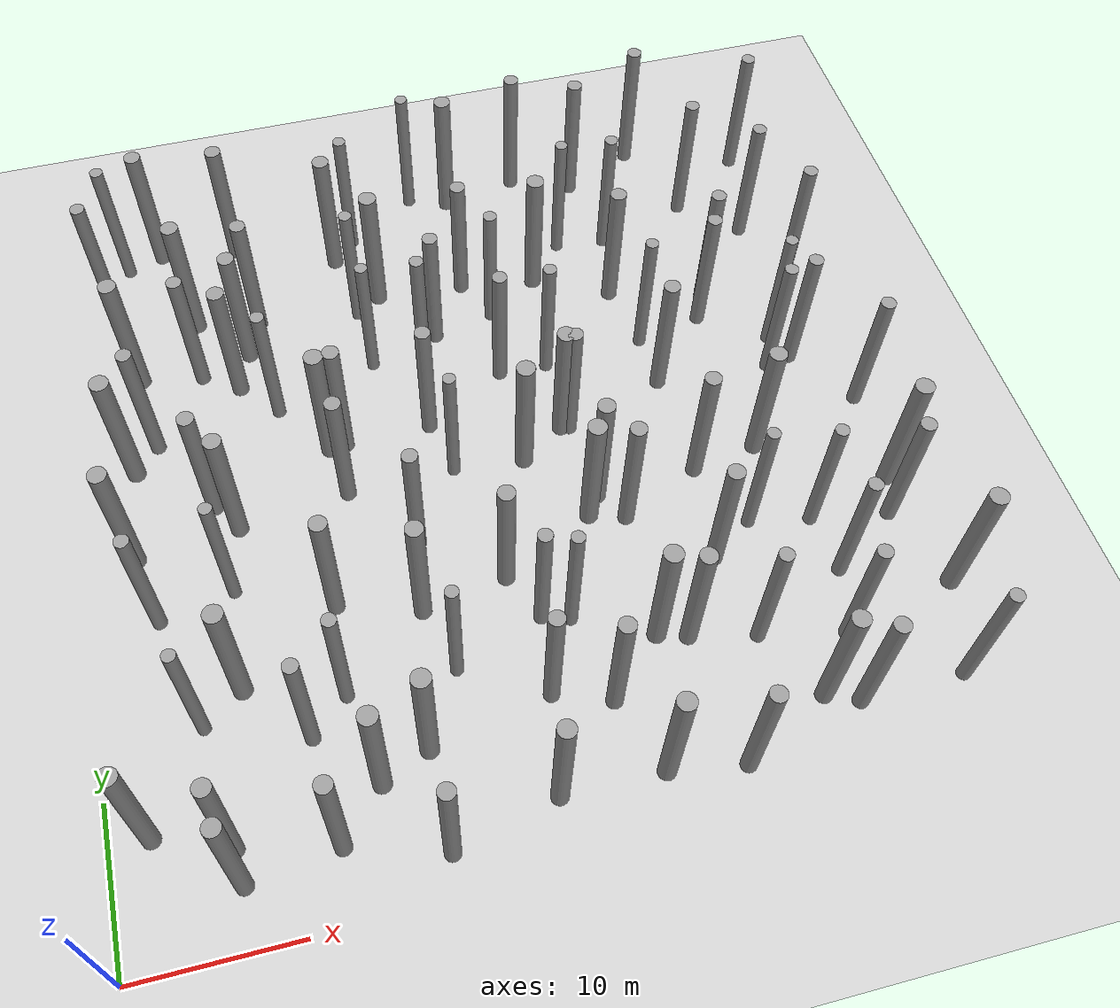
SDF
<?xml version="1.0" ?>
<sdf version="1.5">
    <world name="default">
    <!-- A global light source -->
    <include>
        <uri>model://sun</uri>
    </include>
    <!-- A ground plane -->
    <include>
        <uri>model://ground_plane</uri>
    </include>
    <include>
        <uri>model://asphalt_plane</uri>
    </include>

    <model name='unit_cylinder_0'>
      <pose>6.78198 5.60317 5.02000 0 -0 0</pose>
      <link name='link'>
        <inertial>
          <mass>100</mass>
          <inertia>
            <ixx>20</ixx>
            <ixy>0</ixy>
            <ixz>0</ixz>
            <iyy>20</iyy>
            <iyz>0</iyz>
            <izz>20</izz>
          </inertia>
          <pose>0 0 0 0 -0 0</pose>
        </inertial>
        <collision name='collision'>
          <geometry>
            <cylinder>
              <radius>0.523</radius>
              <length>10.000</length>
            </cylinder>
          </geometry>
          <max_contacts>10</max_contacts>
          <surface>
            <contact>
              <ode/>
            </contact>
            <bounce/>
            <friction>
              <torsional>
                <ode/>
              </torsional>
              <ode/>
            </friction>
          </surface>
        </collision>
        <visual name='visual'>
          <geometry>
            <cylinder>
              <radius>0.523</radius>
              <length>10.000</length>
            </cylinder>
          </geometry>
          <material>
            <script>
              <name>Gazebo/Grey</name>
              <uri>file://media/materials/scripts/gazebo.material</uri>
            </script>
          </material>
        </visual>
        <self_collide>0</self_collide>
        <enable_wind>0</enable_wind>
        <kinematic>0</kinematic>
      </link>
    </model>

    <model name='unit_cylinder_1'>
      <pose>7.00327 3.52950 5.02000 0 -0 0</pose>
      <link name='link'>
        <inertial>
          <mass>100</mass>
          <inertia>
            <ixx>20</ixx>
            <ixy>0</ixy>
            <ixz>0</ixz>
            <iyy>20</iyy>
            <iyz>0</iyz>
            <izz>20</izz>
          </inertia>
          <pose>0 0 0 0 -0 0</pose>
        </inertial>
        <collision name='collision'>
          <geometry>
            <cylinder>
              <radius>0.523</radius>
              <length>10.000</length>
            </cylinder>
          </geometry>
          <max_contacts>10</max_contacts>
          <surface>
            <contact>
              <ode/>
            </contact>
            <bounce/>
            <friction>
              <torsional>
                <ode/>
              </torsional>
              <ode/>
            </friction>
          </surface>
        </collision>
        <visual name='visual'>
          <geometry>
            <cylinder>
              <radius>0.523</radius>
              <length>10.000</length>
            </cylinder>
          </geometry>
          <material>
            <script>
              <name>Gazebo/Grey</name>
              <uri>file://media/materials/scripts/gazebo.material</uri>
            </script>
          </material>
        </visual>
        <self_collide>0</self_collide>
        <enable_wind>0</enable_wind>
        <kinematic>0</kinematic>
      </link>
    </model>

    <model name='unit_cylinder_2'>
      <pose>12.53884 4.29364 5.02000 0 -0 0</pose>
      <link name='link'>
        <inertial>
          <mass>100</mass>
          <inertia>
            <ixx>20</ixx>
            <ixy>0</ixy>
            <ixz>0</ixz>
            <iyy>20</iyy>
            <iyz>0</iyz>
            <izz>20</izz>
          </inertia>
          <pose>0 0 0 0 -0 0</pose>
        </inertial>
        <collision name='collision'>
          <geometry>
            <cylinder>
              <radius>0.518</radius>
              <length>10.000</length>
            </cylinder>
          </geometry>
          <max_contacts>10</max_contacts>
          <surface>
            <contact>
              <ode/>
            </contact>
            <bounce/>
            <friction>
              <torsional>
                <ode/>
              </torsional>
              <ode/>
            </friction>
          </surface>
        </collision>
        <visual name='visual'>
          <geometry>
            <cylinder>
              <radius>0.518</radius>
              <length>10.000</length>
            </cylinder>
          </geometry>
          <material>
            <script>
              <name>Gazebo/Grey</name>
              <uri>file://media/materials/scripts/gazebo.material</uri>
            </script>
          </material>
        </visual>
        <self_collide>0</self_collide>
        <enable_wind>0</enable_wind>
        <kinematic>0</kinematic>
      </link>
    </model>

    <model name='unit_cylinder_3'>
      <pose>18.27836 2.49734 5.02000 0 -0 0</pose>
      <link name='link'>
        <inertial>
          <mass>100</mass>
          <inertia>
            <ixx>20</ixx>
            <ixy>0</ixy>
            <ixz>0</ixz>
            <iyy>20</iyy>
            <iyz>0</iyz>
            <izz>20</izz>
          </inertia>
          <pose>0 0 0 0 -0 0</pose>
        </inertial>
        <collision name='collision'>
          <geometry>
            <cylinder>
              <radius>0.497</radius>
              <length>10.000</length>
            </cylinder>
          </geometry>
          <max_contacts>10</max_contacts>
          <surface>
            <contact>
              <ode/>
            </contact>
            <bounce/>
            <friction>
              <torsional>
                <ode/>
              </torsional>
              <ode/>
            </friction>
          </surface>
        </collision>
        <visual name='visual'>
          <geometry>
            <cylinder>
              <radius>0.497</radius>
              <length>10.000</length>
            </cylinder>
          </geometry>
          <material>
            <script>
              <name>Gazebo/Grey</name>
              <uri>file://media/materials/scripts/gazebo.material</uri>
            </script>
          </material>
        </visual>
        <self_collide>0</self_collide>
        <enable_wind>0</enable_wind>
        <kinematic>0</kinematic>
      </link>
    </model>

    <model name='unit_cylinder_4'>
      <pose>24.80579 4.12080 5.02000 0 -0 0</pose>
      <link name='link'>
        <inertial>
          <mass>100</mass>
          <inertia>
            <ixx>20</ixx>
            <ixy>0</ixy>
            <ixz>0</ixz>
            <iyy>20</iyy>
            <iyz>0</iyz>
            <izz>20</izz>
          </inertia>
          <pose>0 0 0 0 -0 0</pose>
        </inertial>
        <collision name='collision'>
          <geometry>
            <cylinder>
              <radius>0.541</radius>
              <length>10.000</length>
            </cylinder>
          </geometry>
          <max_contacts>10</max_contacts>
          <surface>
            <contact>
              <ode/>
            </contact>
            <bounce/>
            <friction>
              <torsional>
                <ode/>
              </torsional>
              <ode/>
            </friction>
          </surface>
        </collision>
        <visual name='visual'>
          <geometry>
            <cylinder>
              <radius>0.541</radius>
              <length>10.000</length>
            </cylinder>
          </geometry>
          <material>
            <script>
              <name>Gazebo/Grey</name>
              <uri>file://media/materials/scripts/gazebo.material</uri>
            </script>
          </material>
        </visual>
        <self_collide>0</self_collide>
        <enable_wind>0</enable_wind>
        <kinematic>0</kinematic>
      </link>
    </model>

    <model name='unit_cylinder_5'>
      <pose>31.07888 4.03322 5.02000 0 -0 0</pose>
      <link name='link'>
        <inertial>
          <mass>100</mass>
          <inertia>
            <ixx>20</ixx>
            <ixy>0</ixy>
            <ixz>0</ixz>
            <iyy>20</iyy>
            <iyz>0</iyz>
            <izz>20</izz>
          </inertia>
          <pose>0 0 0 0 -0 0</pose>
        </inertial>
        <collision name='collision'>
          <geometry>
            <cylinder>
              <radius>0.566</radius>
              <length>10.000</length>
            </cylinder>
          </geometry>
          <max_contacts>10</max_contacts>
          <surface>
            <contact>
              <ode/>
            </contact>
            <bounce/>
            <friction>
              <torsional>
                <ode/>
              </torsional>
              <ode/>
            </friction>
          </surface>
        </collision>
        <visual name='visual'>
          <geometry>
            <cylinder>
              <radius>0.566</radius>
              <length>10.000</length>
            </cylinder>
          </geometry>
          <material>
            <script>
              <name>Gazebo/Grey</name>
              <uri>file://media/materials/scripts/gazebo.material</uri>
            </script>
          </material>
        </visual>
        <self_collide>0</self_collide>
        <enable_wind>0</enable_wind>
        <kinematic>0</kinematic>
      </link>
    </model>

    <model name='unit_cylinder_6'>
      <pose>35.71000 3.27788 5.02000 0 -0 0</pose>
      <link name='link'>
        <inertial>
          <mass>100</mass>
          <inertia>
            <ixx>20</ixx>
            <ixy>0</ixy>
            <ixz>0</ixz>
            <iyy>20</iyy>
            <iyz>0</iyz>
            <izz>20</izz>
          </inertia>
          <pose>0 0 0 0 -0 0</pose>
        </inertial>
        <collision name='collision'>
          <geometry>
            <cylinder>
              <radius>0.510</radius>
              <length>10.000</length>
            </cylinder>
          </geometry>
          <max_contacts>10</max_contacts>
          <surface>
            <contact>
              <ode/>
            </contact>
            <bounce/>
            <friction>
              <torsional>
                <ode/>
              </torsional>
              <ode/>
            </friction>
          </surface>
        </collision>
        <visual name='visual'>
          <geometry>
            <cylinder>
              <radius>0.510</radius>
              <length>10.000</length>
            </cylinder>
          </geometry>
          <material>
            <script>
              <name>Gazebo/Grey</name>
              <uri>file://media/materials/scripts/gazebo.material</uri>
            </script>
          </material>
        </visual>
        <self_collide>0</self_collide>
        <enable_wind>0</enable_wind>
        <kinematic>0</kinematic>
      </link>
    </model>

    <model name='unit_cylinder_7'>
      <pose>41.43956 6.17991 5.02000 0 -0 0</pose>
      <link name='link'>
        <inertial>
          <mass>100</mass>
          <inertia>
            <ixx>20</ixx>
            <ixy>0</ixy>
            <ixz>0</ixz>
            <iyy>20</iyy>
            <iyz>0</iyz>
            <izz>20</izz>
          </inertia>
          <pose>0 0 0 0 -0 0</pose>
        </inertial>
        <collision name='collision'>
          <geometry>
            <cylinder>
              <radius>0.551</radius>
              <length>10.000</length>
            </cylinder>
          </geometry>
          <max_contacts>10</max_contacts>
          <surface>
            <contact>
              <ode/>
            </contact>
            <bounce/>
            <friction>
              <torsional>
                <ode/>
              </torsional>
              <ode/>
            </friction>
          </surface>
        </collision>
        <visual name='visual'>
          <geometry>
            <cylinder>
              <radius>0.551</radius>
              <length>10.000</length>
            </cylinder>
          </geometry>
          <material>
            <script>
              <name>Gazebo/Grey</name>
              <uri>file://media/materials/scripts/gazebo.material</uri>
            </script>
          </material>
        </visual>
        <self_collide>0</self_collide>
        <enable_wind>0</enable_wind>
        <kinematic>0</kinematic>
      </link>
    </model>

    <model name='unit_cylinder_8'>
      <pose>43.38921 5.31190 5.02000 0 -0 0</pose>
      <link name='link'>
        <inertial>
          <mass>100</mass>
          <inertia>
            <ixx>20</ixx>
            <ixy>0</ixy>
            <ixz>0</ixz>
            <iyy>20</iyy>
            <iyz>0</iyz>
            <izz>20</izz>
          </inertia>
          <pose>0 0 0 0 -0 0</pose>
        </inertial>
        <collision name='collision'>
          <geometry>
            <cylinder>
              <radius>0.507</radius>
              <length>10.000</length>
            </cylinder>
          </geometry>
          <max_contacts>10</max_contacts>
          <surface>
            <contact>
              <ode/>
            </contact>
            <bounce/>
            <friction>
              <torsional>
                <ode/>
              </torsional>
              <ode/>
            </friction>
          </surface>
        </collision>
        <visual name='visual'>
          <geometry>
            <cylinder>
              <radius>0.507</radius>
              <length>10.000</length>
            </cylinder>
          </geometry>
          <material>
            <script>
              <name>Gazebo/Grey</name>
              <uri>file://media/materials/scripts/gazebo.material</uri>
            </script>
          </material>
        </visual>
        <self_collide>0</self_collide>
        <enable_wind>0</enable_wind>
        <kinematic>0</kinematic>
      </link>
    </model>

    <model name='unit_cylinder_9'>
      <pose>49.97748 5.42554 5.02000 0 -0 0</pose>
      <link name='link'>
        <inertial>
          <mass>100</mass>
          <inertia>
            <ixx>20</ixx>
            <ixy>0</ixy>
            <ixz>0</ixz>
            <iyy>20</iyy>
            <iyz>0</iyz>
            <izz>20</izz>
          </inertia>
          <pose>0 0 0 0 -0 0</pose>
        </inertial>
        <collision name='collision'>
          <geometry>
            <cylinder>
              <radius>0.439</radius>
              <length>10.000</length>
            </cylinder>
          </geometry>
          <max_contacts>10</max_contacts>
          <surface>
            <contact>
              <ode/>
            </contact>
            <bounce/>
            <friction>
              <torsional>
                <ode/>
              </torsional>
              <ode/>
            </friction>
          </surface>
        </collision>
        <visual name='visual'>
          <geometry>
            <cylinder>
              <radius>0.439</radius>
              <length>10.000</length>
            </cylinder>
          </geometry>
          <material>
            <script>
              <name>Gazebo/Grey</name>
              <uri>file://media/materials/scripts/gazebo.material</uri>
            </script>
          </material>
        </visual>
        <self_collide>0</self_collide>
        <enable_wind>0</enable_wind>
        <kinematic>0</kinematic>
      </link>
    </model>

    <model name='unit_cylinder_10'>
      <pose>2.38377 7.27922 5.02000 0 -0 0</pose>
      <link name='link'>
        <inertial>
          <mass>100</mass>
          <inertia>
            <ixx>20</ixx>
            <ixy>0</ixy>
            <ixz>0</ixz>
            <iyy>20</iyy>
            <iyz>0</iyz>
            <izz>20</izz>
          </inertia>
          <pose>0 0 0 0 -0 0</pose>
        </inertial>
        <collision name='collision'>
          <geometry>
            <cylinder>
              <radius>0.546</radius>
              <length>10.000</length>
            </cylinder>
          </geometry>
          <max_contacts>10</max_contacts>
          <surface>
            <contact>
              <ode/>
            </contact>
            <bounce/>
            <friction>
              <torsional>
                <ode/>
              </torsional>
              <ode/>
            </friction>
          </surface>
        </collision>
        <visual name='visual'>
          <geometry>
            <cylinder>
              <radius>0.546</radius>
              <length>10.000</length>
            </cylinder>
          </geometry>
          <material>
            <script>
              <name>Gazebo/Grey</name>
              <uri>file://media/materials/scripts/gazebo.material</uri>
            </script>
          </material>
        </visual>
        <self_collide>0</self_collide>
        <enable_wind>0</enable_wind>
        <kinematic>0</kinematic>
      </link>
    </model>

    <model name='unit_cylinder_11'>
      <pose>11.96303 10.88422 5.02000 0 -0 0</pose>
      <link name='link'>
        <inertial>
          <mass>100</mass>
          <inertia>
            <ixx>20</ixx>
            <ixy>0</ixy>
            <ixz>0</ixz>
            <iyy>20</iyy>
            <iyz>0</iyz>
            <izz>20</izz>
          </inertia>
          <pose>0 0 0 0 -0 0</pose>
        </inertial>
        <collision name='collision'>
          <geometry>
            <cylinder>
              <radius>0.463</radius>
              <length>10.000</length>
            </cylinder>
          </geometry>
          <max_contacts>10</max_contacts>
          <surface>
            <contact>
              <ode/>
            </contact>
            <bounce/>
            <friction>
              <torsional>
                <ode/>
              </torsional>
              <ode/>
            </friction>
          </surface>
        </collision>
        <visual name='visual'>
          <geometry>
            <cylinder>
              <radius>0.463</radius>
              <length>10.000</length>
            </cylinder>
          </geometry>
          <material>
            <script>
              <name>Gazebo/Grey</name>
              <uri>file://media/materials/scripts/gazebo.material</uri>
            </script>
          </material>
        </visual>
        <self_collide>0</self_collide>
        <enable_wind>0</enable_wind>
        <kinematic>0</kinematic>
      </link>
    </model>

    <model name='unit_cylinder_12'>
      <pose>15.30151 7.25706 5.02000 0 -0 0</pose>
      <link name='link'>
        <inertial>
          <mass>100</mass>
          <inertia>
            <ixx>20</ixx>
            <ixy>0</ixy>
            <ixz>0</ixz>
            <iyy>20</iyy>
            <iyz>0</iyz>
            <izz>20</izz>
          </inertia>
          <pose>0 0 0 0 -0 0</pose>
        </inertial>
        <collision name='collision'>
          <geometry>
            <cylinder>
              <radius>0.576</radius>
              <length>10.000</length>
            </cylinder>
          </geometry>
          <max_contacts>10</max_contacts>
          <surface>
            <contact>
              <ode/>
            </contact>
            <bounce/>
            <friction>
              <torsional>
                <ode/>
              </torsional>
              <ode/>
            </friction>
          </surface>
        </collision>
        <visual name='visual'>
          <geometry>
            <cylinder>
              <radius>0.576</radius>
              <length>10.000</length>
            </cylinder>
          </geometry>
          <material>
            <script>
              <name>Gazebo/Grey</name>
              <uri>file://media/materials/scripts/gazebo.material</uri>
            </script>
          </material>
        </visual>
        <self_collide>0</self_collide>
        <enable_wind>0</enable_wind>
        <kinematic>0</kinematic>
      </link>
    </model>

    <model name='unit_cylinder_13'>
      <pose>18.31864 8.57995 5.02000 0 -0 0</pose>
      <link name='link'>
        <inertial>
          <mass>100</mass>
          <inertia>
            <ixx>20</ixx>
            <ixy>0</ixy>
            <ixz>0</ixz>
            <iyy>20</iyy>
            <iyz>0</iyz>
            <izz>20</izz>
          </inertia>
          <pose>0 0 0 0 -0 0</pose>
        </inertial>
        <collision name='collision'>
          <geometry>
            <cylinder>
              <radius>0.579</radius>
              <length>10.000</length>
            </cylinder>
          </geometry>
          <max_contacts>10</max_contacts>
          <surface>
            <contact>
              <ode/>
            </contact>
            <bounce/>
            <friction>
              <torsional>
                <ode/>
              </torsional>
              <ode/>
            </friction>
          </surface>
        </collision>
        <visual name='visual'>
          <geometry>
            <cylinder>
              <radius>0.579</radius>
              <length>10.000</length>
            </cylinder>
          </geometry>
          <material>
            <script>
              <name>Gazebo/Grey</name>
              <uri>file://media/materials/scripts/gazebo.material</uri>
            </script>
          </material>
        </visual>
        <self_collide>0</self_collide>
        <enable_wind>0</enable_wind>
        <kinematic>0</kinematic>
      </link>
    </model>

    <model name='unit_cylinder_14'>
      <pose>25.96653 10.12796 5.02000 0 -0 0</pose>
      <link name='link'>
        <inertial>
          <mass>100</mass>
          <inertia>
            <ixx>20</ixx>
            <ixy>0</ixy>
            <ixz>0</ixz>
            <iyy>20</iyy>
            <iyz>0</iyz>
            <izz>20</izz>
          </inertia>
          <pose>0 0 0 0 -0 0</pose>
        </inertial>
        <collision name='collision'>
          <geometry>
            <cylinder>
              <radius>0.497</radius>
              <length>10.000</length>
            </cylinder>
          </geometry>
          <max_contacts>10</max_contacts>
          <surface>
            <contact>
              <ode/>
            </contact>
            <bounce/>
            <friction>
              <torsional>
                <ode/>
              </torsional>
              <ode/>
            </friction>
          </surface>
        </collision>
        <visual name='visual'>
          <geometry>
            <cylinder>
              <radius>0.497</radius>
              <length>10.000</length>
            </cylinder>
          </geometry>
          <material>
            <script>
              <name>Gazebo/Grey</name>
              <uri>file://media/materials/scripts/gazebo.material</uri>
            </script>
          </material>
        </visual>
        <self_collide>0</self_collide>
        <enable_wind>0</enable_wind>
        <kinematic>0</kinematic>
      </link>
    </model>

    <model name='unit_cylinder_15'>
      <pose>29.43761 8.84682 5.02000 0 -0 0</pose>
      <link name='link'>
        <inertial>
          <mass>100</mass>
          <inertia>
            <ixx>20</ixx>
            <ixy>0</ixy>
            <ixz>0</ixz>
            <iyy>20</iyy>
            <iyz>0</iyz>
            <izz>20</izz>
          </inertia>
          <pose>0 0 0 0 -0 0</pose>
        </inertial>
        <collision name='collision'>
          <geometry>
            <cylinder>
              <radius>0.524</radius>
              <length>10.000</length>
            </cylinder>
          </geometry>
          <max_contacts>10</max_contacts>
          <surface>
            <contact>
              <ode/>
            </contact>
            <bounce/>
            <friction>
              <torsional>
                <ode/>
              </torsional>
              <ode/>
            </friction>
          </surface>
        </collision>
        <visual name='visual'>
          <geometry>
            <cylinder>
              <radius>0.524</radius>
              <length>10.000</length>
            </cylinder>
          </geometry>
          <material>
            <script>
              <name>Gazebo/Grey</name>
              <uri>file://media/materials/scripts/gazebo.material</uri>
            </script>
          </material>
        </visual>
        <self_collide>0</self_collide>
        <enable_wind>0</enable_wind>
        <kinematic>0</kinematic>
      </link>
    </model>

    <model name='unit_cylinder_16'>
      <pose>34.93175 11.71264 5.02000 0 -0 0</pose>
      <link name='link'>
        <inertial>
          <mass>100</mass>
          <inertia>
            <ixx>20</ixx>
            <ixy>0</ixy>
            <ixz>0</ixz>
            <iyy>20</iyy>
            <iyz>0</iyz>
            <izz>20</izz>
          </inertia>
          <pose>0 0 0 0 -0 0</pose>
        </inertial>
        <collision name='collision'>
          <geometry>
            <cylinder>
              <radius>0.543</radius>
              <length>10.000</length>
            </cylinder>
          </geometry>
          <max_contacts>10</max_contacts>
          <surface>
            <contact>
              <ode/>
            </contact>
            <bounce/>
            <friction>
              <torsional>
                <ode/>
              </torsional>
              <ode/>
            </friction>
          </surface>
        </collision>
        <visual name='visual'>
          <geometry>
            <cylinder>
              <radius>0.543</radius>
              <length>10.000</length>
            </cylinder>
          </geometry>
          <material>
            <script>
              <name>Gazebo/Grey</name>
              <uri>file://media/materials/scripts/gazebo.material</uri>
            </script>
          </material>
        </visual>
        <self_collide>0</self_collide>
        <enable_wind>0</enable_wind>
        <kinematic>0</kinematic>
      </link>
    </model>

    <model name='unit_cylinder_17'>
      <pose>39.03436 10.75509 5.02000 0 -0 0</pose>
      <link name='link'>
        <inertial>
          <mass>100</mass>
          <inertia>
            <ixx>20</ixx>
            <ixy>0</ixy>
            <ixz>0</ixz>
            <iyy>20</iyy>
            <iyz>0</iyz>
            <izz>20</izz>
          </inertia>
          <pose>0 0 0 0 -0 0</pose>
        </inertial>
        <collision name='collision'>
          <geometry>
            <cylinder>
              <radius>0.458</radius>
              <length>10.000</length>
            </cylinder>
          </geometry>
          <max_contacts>10</max_contacts>
          <surface>
            <contact>
              <ode/>
            </contact>
            <bounce/>
            <friction>
              <torsional>
                <ode/>
              </torsional>
              <ode/>
            </friction>
          </surface>
        </collision>
        <visual name='visual'>
          <geometry>
            <cylinder>
              <radius>0.458</radius>
              <length>10.000</length>
            </cylinder>
          </geometry>
          <material>
            <script>
              <name>Gazebo/Grey</name>
              <uri>file://media/materials/scripts/gazebo.material</uri>
            </script>
          </material>
        </visual>
        <self_collide>0</self_collide>
        <enable_wind>0</enable_wind>
        <kinematic>0</kinematic>
      </link>
    </model>

    <model name='unit_cylinder_18'>
      <pose>44.28129 9.62120 5.02000 0 -0 0</pose>
      <link name='link'>
        <inertial>
          <mass>100</mass>
          <inertia>
            <ixx>20</ixx>
            <ixy>0</ixy>
            <ixz>0</ixz>
            <iyy>20</iyy>
            <iyz>0</iyz>
            <izz>20</izz>
          </inertia>
          <pose>0 0 0 0 -0 0</pose>
        </inertial>
        <collision name='collision'>
          <geometry>
            <cylinder>
              <radius>0.467</radius>
              <length>10.000</length>
            </cylinder>
          </geometry>
          <max_contacts>10</max_contacts>
          <surface>
            <contact>
              <ode/>
            </contact>
            <bounce/>
            <friction>
              <torsional>
                <ode/>
              </torsional>
              <ode/>
            </friction>
          </surface>
        </collision>
        <visual name='visual'>
          <geometry>
            <cylinder>
              <radius>0.467</radius>
              <length>10.000</length>
            </cylinder>
          </geometry>
          <material>
            <script>
              <name>Gazebo/Grey</name>
              <uri>file://media/materials/scripts/gazebo.material</uri>
            </script>
          </material>
        </visual>
        <self_collide>0</self_collide>
        <enable_wind>0</enable_wind>
        <kinematic>0</kinematic>
      </link>
    </model>

    <model name='unit_cylinder_19'>
      <pose>51.85830 11.31948 5.02000 0 -0 0</pose>
      <link name='link'>
        <inertial>
          <mass>100</mass>
          <inertia>
            <ixx>20</ixx>
            <ixy>0</ixy>
            <ixz>0</ixz>
            <iyy>20</iyy>
            <iyz>0</iyz>
            <izz>20</izz>
          </inertia>
          <pose>0 0 0 0 -0 0</pose>
        </inertial>
        <collision name='collision'>
          <geometry>
            <cylinder>
              <radius>0.586</radius>
              <length>10.000</length>
            </cylinder>
          </geometry>
          <max_contacts>10</max_contacts>
          <surface>
            <contact>
              <ode/>
            </contact>
            <bounce/>
            <friction>
              <torsional>
                <ode/>
              </torsional>
              <ode/>
            </friction>
          </surface>
        </collision>
        <visual name='visual'>
          <geometry>
            <cylinder>
              <radius>0.586</radius>
              <length>10.000</length>
            </cylinder>
          </geometry>
          <material>
            <script>
              <name>Gazebo/Grey</name>
              <uri>file://media/materials/scripts/gazebo.material</uri>
            </script>
          </material>
        </visual>
        <self_collide>0</self_collide>
        <enable_wind>0</enable_wind>
        <kinematic>0</kinematic>
      </link>
    </model>

    <model name='unit_cylinder_20'>
      <pose>5.97836 13.00157 5.02000 0 -0 0</pose>
      <link name='link'>
        <inertial>
          <mass>100</mass>
          <inertia>
            <ixx>20</ixx>
            <ixy>0</ixy>
            <ixz>0</ixz>
            <iyy>20</iyy>
            <iyz>0</iyz>
            <izz>20</izz>
          </inertia>
          <pose>0 0 0 0 -0 0</pose>
        </inertial>
        <collision name='collision'>
          <geometry>
            <cylinder>
              <radius>0.407</radius>
              <length>10.000</length>
            </cylinder>
          </geometry>
          <max_contacts>10</max_contacts>
          <surface>
            <contact>
              <ode/>
            </contact>
            <bounce/>
            <friction>
              <torsional>
                <ode/>
              </torsional>
              <ode/>
            </friction>
          </surface>
        </collision>
        <visual name='visual'>
          <geometry>
            <cylinder>
              <radius>0.407</radius>
              <length>10.000</length>
            </cylinder>
          </geometry>
          <material>
            <script>
              <name>Gazebo/Grey</name>
              <uri>file://media/materials/scripts/gazebo.material</uri>
            </script>
          </material>
        </visual>
        <self_collide>0</self_collide>
        <enable_wind>0</enable_wind>
        <kinematic>0</kinematic>
      </link>
    </model>

    <model name='unit_cylinder_21'>
      <pose>8.47928 14.81799 5.02000 0 -0 0</pose>
      <link name='link'>
        <inertial>
          <mass>100</mass>
          <inertia>
            <ixx>20</ixx>
            <ixy>0</ixy>
            <ixz>0</ixz>
            <iyy>20</iyy>
            <iyz>0</iyz>
            <izz>20</izz>
          </inertia>
          <pose>0 0 0 0 -0 0</pose>
        </inertial>
        <collision name='collision'>
          <geometry>
            <cylinder>
              <radius>0.591</radius>
              <length>10.000</length>
            </cylinder>
          </geometry>
          <max_contacts>10</max_contacts>
          <surface>
            <contact>
              <ode/>
            </contact>
            <bounce/>
            <friction>
              <torsional>
                <ode/>
              </torsional>
              <ode/>
            </friction>
          </surface>
        </collision>
        <visual name='visual'>
          <geometry>
            <cylinder>
              <radius>0.591</radius>
              <length>10.000</length>
            </cylinder>
          </geometry>
          <material>
            <script>
              <name>Gazebo/Grey</name>
              <uri>file://media/materials/scripts/gazebo.material</uri>
            </script>
          </material>
        </visual>
        <self_collide>0</self_collide>
        <enable_wind>0</enable_wind>
        <kinematic>0</kinematic>
      </link>
    </model>

    <model name='unit_cylinder_22'>
      <pose>14.33526 12.97418 5.02000 0 -0 0</pose>
      <link name='link'>
        <inertial>
          <mass>100</mass>
          <inertia>
            <ixx>20</ixx>
            <ixy>0</ixy>
            <ixz>0</ixz>
            <iyy>20</iyy>
            <iyz>0</iyz>
            <izz>20</izz>
          </inertia>
          <pose>0 0 0 0 -0 0</pose>
        </inertial>
        <collision name='collision'>
          <geometry>
            <cylinder>
              <radius>0.434</radius>
              <length>10.000</length>
            </cylinder>
          </geometry>
          <max_contacts>10</max_contacts>
          <surface>
            <contact>
              <ode/>
            </contact>
            <bounce/>
            <friction>
              <torsional>
                <ode/>
              </torsional>
              <ode/>
            </friction>
          </surface>
        </collision>
        <visual name='visual'>
          <geometry>
            <cylinder>
              <radius>0.434</radius>
              <length>10.000</length>
            </cylinder>
          </geometry>
          <material>
            <script>
              <name>Gazebo/Grey</name>
              <uri>file://media/materials/scripts/gazebo.material</uri>
            </script>
          </material>
        </visual>
        <self_collide>0</self_collide>
        <enable_wind>0</enable_wind>
        <kinematic>0</kinematic>
      </link>
    </model>

    <model name='unit_cylinder_23'>
      <pose>20.95681 13.01195 5.02000 0 -0 0</pose>
      <link name='link'>
        <inertial>
          <mass>100</mass>
          <inertia>
            <ixx>20</ixx>
            <ixy>0</ixy>
            <ixz>0</ixz>
            <iyy>20</iyy>
            <iyz>0</iyz>
            <izz>20</izz>
          </inertia>
          <pose>0 0 0 0 -0 0</pose>
        </inertial>
        <collision name='collision'>
          <geometry>
            <cylinder>
              <radius>0.402</radius>
              <length>10.000</length>
            </cylinder>
          </geometry>
          <max_contacts>10</max_contacts>
          <surface>
            <contact>
              <ode/>
            </contact>
            <bounce/>
            <friction>
              <torsional>
                <ode/>
              </torsional>
              <ode/>
            </friction>
          </surface>
        </collision>
        <visual name='visual'>
          <geometry>
            <cylinder>
              <radius>0.402</radius>
              <length>10.000</length>
            </cylinder>
          </geometry>
          <material>
            <script>
              <name>Gazebo/Grey</name>
              <uri>file://media/materials/scripts/gazebo.material</uri>
            </script>
          </material>
        </visual>
        <self_collide>0</self_collide>
        <enable_wind>0</enable_wind>
        <kinematic>0</kinematic>
      </link>
    </model>

    <model name='unit_cylinder_24'>
      <pose>26.69320 15.12144 5.02000 0 -0 0</pose>
      <link name='link'>
        <inertial>
          <mass>100</mass>
          <inertia>
            <ixx>20</ixx>
            <ixy>0</ixy>
            <ixz>0</ixz>
            <iyy>20</iyy>
            <iyz>0</iyz>
            <izz>20</izz>
          </inertia>
          <pose>0 0 0 0 -0 0</pose>
        </inertial>
        <collision name='collision'>
          <geometry>
            <cylinder>
              <radius>0.455</radius>
              <length>10.000</length>
            </cylinder>
          </geometry>
          <max_contacts>10</max_contacts>
          <surface>
            <contact>
              <ode/>
            </contact>
            <bounce/>
            <friction>
              <torsional>
                <ode/>
              </torsional>
              <ode/>
            </friction>
          </surface>
        </collision>
        <visual name='visual'>
          <geometry>
            <cylinder>
              <radius>0.455</radius>
              <length>10.000</length>
            </cylinder>
          </geometry>
          <material>
            <script>
              <name>Gazebo/Grey</name>
              <uri>file://media/materials/scripts/gazebo.material</uri>
            </script>
          </material>
        </visual>
        <self_collide>0</self_collide>
        <enable_wind>0</enable_wind>
        <kinematic>0</kinematic>
      </link>
    </model>

    <model name='unit_cylinder_25'>
      <pose>28.40187 14.56460 5.02000 0 -0 0</pose>
      <link name='link'>
        <inertial>
          <mass>100</mass>
          <inertia>
            <ixx>20</ixx>
            <ixy>0</ixy>
            <ixz>0</ixz>
            <iyy>20</iyy>
            <iyz>0</iyz>
            <izz>20</izz>
          </inertia>
          <pose>0 0 0 0 -0 0</pose>
        </inertial>
        <collision name='collision'>
          <geometry>
            <cylinder>
              <radius>0.419</radius>
              <length>10.000</length>
            </cylinder>
          </geometry>
          <max_contacts>10</max_contacts>
          <surface>
            <contact>
              <ode/>
            </contact>
            <bounce/>
            <friction>
              <torsional>
                <ode/>
              </torsional>
              <ode/>
            </friction>
          </surface>
        </collision>
        <visual name='visual'>
          <geometry>
            <cylinder>
              <radius>0.419</radius>
              <length>10.000</length>
            </cylinder>
          </geometry>
          <material>
            <script>
              <name>Gazebo/Grey</name>
              <uri>file://media/materials/scripts/gazebo.material</uri>
            </script>
          </material>
        </visual>
        <self_collide>0</self_collide>
        <enable_wind>0</enable_wind>
        <kinematic>0</kinematic>
      </link>
    </model>

    <model name='unit_cylinder_26'>
      <pose>33.13048 12.30759 5.02000 0 -0 0</pose>
      <link name='link'>
        <inertial>
          <mass>100</mass>
          <inertia>
            <ixx>20</ixx>
            <ixy>0</ixy>
            <ixz>0</ixz>
            <iyy>20</iyy>
            <iyz>0</iyz>
            <izz>20</izz>
          </inertia>
          <pose>0 0 0 0 -0 0</pose>
        </inertial>
        <collision name='collision'>
          <geometry>
            <cylinder>
              <radius>0.591</radius>
              <length>10.000</length>
            </cylinder>
          </geometry>
          <max_contacts>10</max_contacts>
          <surface>
            <contact>
              <ode/>
            </contact>
            <bounce/>
            <friction>
              <torsional>
                <ode/>
              </torsional>
              <ode/>
            </friction>
          </surface>
        </collision>
        <visual name='visual'>
          <geometry>
            <cylinder>
              <radius>0.591</radius>
              <length>10.000</length>
            </cylinder>
          </geometry>
          <material>
            <script>
              <name>Gazebo/Grey</name>
              <uri>file://media/materials/scripts/gazebo.material</uri>
            </script>
          </material>
        </visual>
        <self_collide>0</self_collide>
        <enable_wind>0</enable_wind>
        <kinematic>0</kinematic>
      </link>
    </model>

    <model name='unit_cylinder_27'>
      <pose>38.22628 16.43758 5.02000 0 -0 0</pose>
      <link name='link'>
        <inertial>
          <mass>100</mass>
          <inertia>
            <ixx>20</ixx>
            <ixy>0</ixy>
            <ixz>0</ixz>
            <iyy>20</iyy>
            <iyz>0</iyz>
            <izz>20</izz>
          </inertia>
          <pose>0 0 0 0 -0 0</pose>
        </inertial>
        <collision name='collision'>
          <geometry>
            <cylinder>
              <radius>0.539</radius>
              <length>10.000</length>
            </cylinder>
          </geometry>
          <max_contacts>10</max_contacts>
          <surface>
            <contact>
              <ode/>
            </contact>
            <bounce/>
            <friction>
              <torsional>
                <ode/>
              </torsional>
              <ode/>
            </friction>
          </surface>
        </collision>
        <visual name='visual'>
          <geometry>
            <cylinder>
              <radius>0.539</radius>
              <length>10.000</length>
            </cylinder>
          </geometry>
          <material>
            <script>
              <name>Gazebo/Grey</name>
              <uri>file://media/materials/scripts/gazebo.material</uri>
            </script>
          </material>
        </visual>
        <self_collide>0</self_collide>
        <enable_wind>0</enable_wind>
        <kinematic>0</kinematic>
      </link>
    </model>

    <model name='unit_cylinder_28'>
      <pose>45.51048 13.75221 5.02000 0 -0 0</pose>
      <link name='link'>
        <inertial>
          <mass>100</mass>
          <inertia>
            <ixx>20</ixx>
            <ixy>0</ixy>
            <ixz>0</ixz>
            <iyy>20</iyy>
            <iyz>0</iyz>
            <izz>20</izz>
          </inertia>
          <pose>0 0 0 0 -0 0</pose>
        </inertial>
        <collision name='collision'>
          <geometry>
            <cylinder>
              <radius>0.456</radius>
              <length>10.000</length>
            </cylinder>
          </geometry>
          <max_contacts>10</max_contacts>
          <surface>
            <contact>
              <ode/>
            </contact>
            <bounce/>
            <friction>
              <torsional>
                <ode/>
              </torsional>
              <ode/>
            </friction>
          </surface>
        </collision>
        <visual name='visual'>
          <geometry>
            <cylinder>
              <radius>0.456</radius>
              <length>10.000</length>
            </cylinder>
          </geometry>
          <material>
            <script>
              <name>Gazebo/Grey</name>
              <uri>file://media/materials/scripts/gazebo.material</uri>
            </script>
          </material>
        </visual>
        <self_collide>0</self_collide>
        <enable_wind>0</enable_wind>
        <kinematic>0</kinematic>
      </link>
    </model>

    <model name='unit_cylinder_29'>
      <pose>50.10931 16.80766 5.02000 0 -0 0</pose>
      <link name='link'>
        <inertial>
          <mass>100</mass>
          <inertia>
            <ixx>20</ixx>
            <ixy>0</ixy>
            <ixz>0</ixz>
            <iyy>20</iyy>
            <iyz>0</iyz>
            <izz>20</izz>
          </inertia>
          <pose>0 0 0 0 -0 0</pose>
        </inertial>
        <collision name='collision'>
          <geometry>
            <cylinder>
              <radius>0.493</radius>
              <length>10.000</length>
            </cylinder>
          </geometry>
          <max_contacts>10</max_contacts>
          <surface>
            <contact>
              <ode/>
            </contact>
            <bounce/>
            <friction>
              <torsional>
                <ode/>
              </torsional>
              <ode/>
            </friction>
          </surface>
        </collision>
        <visual name='visual'>
          <geometry>
            <cylinder>
              <radius>0.493</radius>
              <length>10.000</length>
            </cylinder>
          </geometry>
          <material>
            <script>
              <name>Gazebo/Grey</name>
              <uri>file://media/materials/scripts/gazebo.material</uri>
            </script>
          </material>
        </visual>
        <self_collide>0</self_collide>
        <enable_wind>0</enable_wind>
        <kinematic>0</kinematic>
      </link>
    </model>

    <model name='unit_cylinder_30'>
      <pose>4.21066 20.43638 5.02000 0 -0 0</pose>
      <link name='link'>
        <inertial>
          <mass>100</mass>
          <inertia>
            <ixx>20</ixx>
            <ixy>0</ixy>
            <ixz>0</ixz>
            <iyy>20</iyy>
            <iyz>0</iyz>
            <izz>20</izz>
          </inertia>
          <pose>0 0 0 0 -0 0</pose>
        </inertial>
        <collision name='collision'>
          <geometry>
            <cylinder>
              <radius>0.449</radius>
              <length>10.000</length>
            </cylinder>
          </geometry>
          <max_contacts>10</max_contacts>
          <surface>
            <contact>
              <ode/>
            </contact>
            <bounce/>
            <friction>
              <torsional>
                <ode/>
              </torsional>
              <ode/>
            </friction>
          </surface>
        </collision>
        <visual name='visual'>
          <geometry>
            <cylinder>
              <radius>0.449</radius>
              <length>10.000</length>
            </cylinder>
          </geometry>
          <material>
            <script>
              <name>Gazebo/Grey</name>
              <uri>file://media/materials/scripts/gazebo.material</uri>
            </script>
          </material>
        </visual>
        <self_collide>0</self_collide>
        <enable_wind>0</enable_wind>
        <kinematic>0</kinematic>
      </link>
    </model>

    <model name='unit_cylinder_31'>
      <pose>8.88682 21.38482 5.02000 0 -0 0</pose>
      <link name='link'>
        <inertial>
          <mass>100</mass>
          <inertia>
            <ixx>20</ixx>
            <ixy>0</ixy>
            <ixz>0</ixz>
            <iyy>20</iyy>
            <iyz>0</iyz>
            <izz>20</izz>
          </inertia>
          <pose>0 0 0 0 -0 0</pose>
        </inertial>
        <collision name='collision'>
          <geometry>
            <cylinder>
              <radius>0.407</radius>
              <length>10.000</length>
            </cylinder>
          </geometry>
          <max_contacts>10</max_contacts>
          <surface>
            <contact>
              <ode/>
            </contact>
            <bounce/>
            <friction>
              <torsional>
                <ode/>
              </torsional>
              <ode/>
            </friction>
          </surface>
        </collision>
        <visual name='visual'>
          <geometry>
            <cylinder>
              <radius>0.407</radius>
              <length>10.000</length>
            </cylinder>
          </geometry>
          <material>
            <script>
              <name>Gazebo/Grey</name>
              <uri>file://media/materials/scripts/gazebo.material</uri>
            </script>
          </material>
        </visual>
        <self_collide>0</self_collide>
        <enable_wind>0</enable_wind>
        <kinematic>0</kinematic>
      </link>
    </model>

    <model name='unit_cylinder_32'>
      <pose>14.76007 18.90415 5.02000 0 -0 0</pose>
      <link name='link'>
        <inertial>
          <mass>100</mass>
          <inertia>
            <ixx>20</ixx>
            <ixy>0</ixy>
            <ixz>0</ixz>
            <iyy>20</iyy>
            <iyz>0</iyz>
            <izz>20</izz>
          </inertia>
          <pose>0 0 0 0 -0 0</pose>
        </inertial>
        <collision name='collision'>
          <geometry>
            <cylinder>
              <radius>0.541</radius>
              <length>10.000</length>
            </cylinder>
          </geometry>
          <max_contacts>10</max_contacts>
          <surface>
            <contact>
              <ode/>
            </contact>
            <bounce/>
            <friction>
              <torsional>
                <ode/>
              </torsional>
              <ode/>
            </friction>
          </surface>
        </collision>
        <visual name='visual'>
          <geometry>
            <cylinder>
              <radius>0.541</radius>
              <length>10.000</length>
            </cylinder>
          </geometry>
          <material>
            <script>
              <name>Gazebo/Grey</name>
              <uri>file://media/materials/scripts/gazebo.material</uri>
            </script>
          </material>
        </visual>
        <self_collide>0</self_collide>
        <enable_wind>0</enable_wind>
        <kinematic>0</kinematic>
      </link>
    </model>

    <model name='unit_cylinder_33'>
      <pose>19.83164 17.28732 5.02000 0 -0 0</pose>
      <link name='link'>
        <inertial>
          <mass>100</mass>
          <inertia>
            <ixx>20</ixx>
            <ixy>0</ixy>
            <ixz>0</ixz>
            <iyy>20</iyy>
            <iyz>0</iyz>
            <izz>20</izz>
          </inertia>
          <pose>0 0 0 0 -0 0</pose>
        </inertial>
        <collision name='collision'>
          <geometry>
            <cylinder>
              <radius>0.552</radius>
              <length>10.000</length>
            </cylinder>
          </geometry>
          <max_contacts>10</max_contacts>
          <surface>
            <contact>
              <ode/>
            </contact>
            <bounce/>
            <friction>
              <torsional>
                <ode/>
              </torsional>
              <ode/>
            </friction>
          </surface>
        </collision>
        <visual name='visual'>
          <geometry>
            <cylinder>
              <radius>0.552</radius>
              <length>10.000</length>
            </cylinder>
          </geometry>
          <material>
            <script>
              <name>Gazebo/Grey</name>
              <uri>file://media/materials/scripts/gazebo.material</uri>
            </script>
          </material>
        </visual>
        <self_collide>0</self_collide>
        <enable_wind>0</enable_wind>
        <kinematic>0</kinematic>
      </link>
    </model>

    <model name='unit_cylinder_34'>
      <pose>25.30924 18.27673 5.02000 0 -0 0</pose>
      <link name='link'>
        <inertial>
          <mass>100</mass>
          <inertia>
            <ixx>20</ixx>
            <ixy>0</ixy>
            <ixz>0</ixz>
            <iyy>20</iyy>
            <iyz>0</iyz>
            <izz>20</izz>
          </inertia>
          <pose>0 0 0 0 -0 0</pose>
        </inertial>
        <collision name='collision'>
          <geometry>
            <cylinder>
              <radius>0.543</radius>
              <length>10.000</length>
            </cylinder>
          </geometry>
          <max_contacts>10</max_contacts>
          <surface>
            <contact>
              <ode/>
            </contact>
            <bounce/>
            <friction>
              <torsional>
                <ode/>
              </torsional>
              <ode/>
            </friction>
          </surface>
        </collision>
        <visual name='visual'>
          <geometry>
            <cylinder>
              <radius>0.543</radius>
              <length>10.000</length>
            </cylinder>
          </geometry>
          <material>
            <script>
              <name>Gazebo/Grey</name>
              <uri>file://media/materials/scripts/gazebo.material</uri>
            </script>
          </material>
        </visual>
        <self_collide>0</self_collide>
        <enable_wind>0</enable_wind>
        <kinematic>0</kinematic>
      </link>
    </model>

    <model name='unit_cylinder_35'>
      <pose>31.51937 21.32872 5.02000 0 -0 0</pose>
      <link name='link'>
        <inertial>
          <mass>100</mass>
          <inertia>
            <ixx>20</ixx>
            <ixy>0</ixy>
            <ixz>0</ixz>
            <iyy>20</iyy>
            <iyz>0</iyz>
            <izz>20</izz>
          </inertia>
          <pose>0 0 0 0 -0 0</pose>
        </inertial>
        <collision name='collision'>
          <geometry>
            <cylinder>
              <radius>0.593</radius>
              <length>10.000</length>
            </cylinder>
          </geometry>
          <max_contacts>10</max_contacts>
          <surface>
            <contact>
              <ode/>
            </contact>
            <bounce/>
            <friction>
              <torsional>
                <ode/>
              </torsional>
              <ode/>
            </friction>
          </surface>
        </collision>
        <visual name='visual'>
          <geometry>
            <cylinder>
              <radius>0.593</radius>
              <length>10.000</length>
            </cylinder>
          </geometry>
          <material>
            <script>
              <name>Gazebo/Grey</name>
              <uri>file://media/materials/scripts/gazebo.material</uri>
            </script>
          </material>
        </visual>
        <self_collide>0</self_collide>
        <enable_wind>0</enable_wind>
        <kinematic>0</kinematic>
      </link>
    </model>

    <model name='unit_cylinder_36'>
      <pose>33.77373 20.61455 5.02000 0 -0 0</pose>
      <link name='link'>
        <inertial>
          <mass>100</mass>
          <inertia>
            <ixx>20</ixx>
            <ixy>0</ixy>
            <ixz>0</ixz>
            <iyy>20</iyy>
            <iyz>0</iyz>
            <izz>20</izz>
          </inertia>
          <pose>0 0 0 0 -0 0</pose>
        </inertial>
        <collision name='collision'>
          <geometry>
            <cylinder>
              <radius>0.526</radius>
              <length>10.000</length>
            </cylinder>
          </geometry>
          <max_contacts>10</max_contacts>
          <surface>
            <contact>
              <ode/>
            </contact>
            <bounce/>
            <friction>
              <torsional>
                <ode/>
              </torsional>
              <ode/>
            </friction>
          </surface>
        </collision>
        <visual name='visual'>
          <geometry>
            <cylinder>
              <radius>0.526</radius>
              <length>10.000</length>
            </cylinder>
          </geometry>
          <material>
            <script>
              <name>Gazebo/Grey</name>
              <uri>file://media/materials/scripts/gazebo.material</uri>
            </script>
          </material>
        </visual>
        <self_collide>0</self_collide>
        <enable_wind>0</enable_wind>
        <kinematic>0</kinematic>
      </link>
    </model>

    <model name='unit_cylinder_37'>
      <pose>41.20551 18.40178 5.02000 0 -0 0</pose>
      <link name='link'>
        <inertial>
          <mass>100</mass>
          <inertia>
            <ixx>20</ixx>
            <ixy>0</ixy>
            <ixz>0</ixz>
            <iyy>20</iyy>
            <iyz>0</iyz>
            <izz>20</izz>
          </inertia>
          <pose>0 0 0 0 -0 0</pose>
        </inertial>
        <collision name='collision'>
          <geometry>
            <cylinder>
              <radius>0.414</radius>
              <length>10.000</length>
            </cylinder>
          </geometry>
          <max_contacts>10</max_contacts>
          <surface>
            <contact>
              <ode/>
            </contact>
            <bounce/>
            <friction>
              <torsional>
                <ode/>
              </torsional>
              <ode/>
            </friction>
          </surface>
        </collision>
        <visual name='visual'>
          <geometry>
            <cylinder>
              <radius>0.414</radius>
              <length>10.000</length>
            </cylinder>
          </geometry>
          <material>
            <script>
              <name>Gazebo/Grey</name>
              <uri>file://media/materials/scripts/gazebo.material</uri>
            </script>
          </material>
        </visual>
        <self_collide>0</self_collide>
        <enable_wind>0</enable_wind>
        <kinematic>0</kinematic>
      </link>
    </model>

    <model name='unit_cylinder_38'>
      <pose>45.11447 17.64728 5.02000 0 -0 0</pose>
      <link name='link'>
        <inertial>
          <mass>100</mass>
          <inertia>
            <ixx>20</ixx>
            <ixy>0</ixy>
            <ixz>0</ixz>
            <iyy>20</iyy>
            <iyz>0</iyz>
            <izz>20</izz>
          </inertia>
          <pose>0 0 0 0 -0 0</pose>
        </inertial>
        <collision name='collision'>
          <geometry>
            <cylinder>
              <radius>0.433</radius>
              <length>10.000</length>
            </cylinder>
          </geometry>
          <max_contacts>10</max_contacts>
          <surface>
            <contact>
              <ode/>
            </contact>
            <bounce/>
            <friction>
              <torsional>
                <ode/>
              </torsional>
              <ode/>
            </friction>
          </surface>
        </collision>
        <visual name='visual'>
          <geometry>
            <cylinder>
              <radius>0.433</radius>
              <length>10.000</length>
            </cylinder>
          </geometry>
          <material>
            <script>
              <name>Gazebo/Grey</name>
              <uri>file://media/materials/scripts/gazebo.material</uri>
            </script>
          </material>
        </visual>
        <self_collide>0</self_collide>
        <enable_wind>0</enable_wind>
        <kinematic>0</kinematic>
      </link>
    </model>

    <model name='unit_cylinder_39'>
      <pose>51.04535 19.37710 5.02000 0 -0 0</pose>
      <link name='link'>
        <inertial>
          <mass>100</mass>
          <inertia>
            <ixx>20</ixx>
            <ixy>0</ixy>
            <ixz>0</ixz>
            <iyy>20</iyy>
            <iyz>0</iyz>
            <izz>20</izz>
          </inertia>
          <pose>0 0 0 0 -0 0</pose>
        </inertial>
        <collision name='collision'>
          <geometry>
            <cylinder>
              <radius>0.591</radius>
              <length>10.000</length>
            </cylinder>
          </geometry>
          <max_contacts>10</max_contacts>
          <surface>
            <contact>
              <ode/>
            </contact>
            <bounce/>
            <friction>
              <torsional>
                <ode/>
              </torsional>
              <ode/>
            </friction>
          </surface>
        </collision>
        <visual name='visual'>
          <geometry>
            <cylinder>
              <radius>0.591</radius>
              <length>10.000</length>
            </cylinder>
          </geometry>
          <material>
            <script>
              <name>Gazebo/Grey</name>
              <uri>file://media/materials/scripts/gazebo.material</uri>
            </script>
          </material>
        </visual>
        <self_collide>0</self_collide>
        <enable_wind>0</enable_wind>
        <kinematic>0</kinematic>
      </link>
    </model>

    <model name='unit_cylinder_40'>
      <pose>3.25371 25.08927 5.02000 0 -0 0</pose>
      <link name='link'>
        <inertial>
          <mass>100</mass>
          <inertia>
            <ixx>20</ixx>
            <ixy>0</ixy>
            <ixz>0</ixz>
            <iyy>20</iyy>
            <iyz>0</iyz>
            <izz>20</izz>
          </inertia>
          <pose>0 0 0 0 -0 0</pose>
        </inertial>
        <collision name='collision'>
          <geometry>
            <cylinder>
              <radius>0.580</radius>
              <length>10.000</length>
            </cylinder>
          </geometry>
          <max_contacts>10</max_contacts>
          <surface>
            <contact>
              <ode/>
            </contact>
            <bounce/>
            <friction>
              <torsional>
                <ode/>
              </torsional>
              <ode/>
            </friction>
          </surface>
        </collision>
        <visual name='visual'>
          <geometry>
            <cylinder>
              <radius>0.580</radius>
              <length>10.000</length>
            </cylinder>
          </geometry>
          <material>
            <script>
              <name>Gazebo/Grey</name>
              <uri>file://media/materials/scripts/gazebo.material</uri>
            </script>
          </material>
        </visual>
        <self_collide>0</self_collide>
        <enable_wind>0</enable_wind>
        <kinematic>0</kinematic>
      </link>
    </model>

    <model name='unit_cylinder_41'>
      <pose>9.79973 25.79322 5.02000 0 -0 0</pose>
      <link name='link'>
        <inertial>
          <mass>100</mass>
          <inertia>
            <ixx>20</ixx>
            <ixy>0</ixy>
            <ixz>0</ixz>
            <iyy>20</iyy>
            <iyz>0</iyz>
            <izz>20</izz>
          </inertia>
          <pose>0 0 0 0 -0 0</pose>
        </inertial>
        <collision name='collision'>
          <geometry>
            <cylinder>
              <radius>0.564</radius>
              <length>10.000</length>
            </cylinder>
          </geometry>
          <max_contacts>10</max_contacts>
          <surface>
            <contact>
              <ode/>
            </contact>
            <bounce/>
            <friction>
              <torsional>
                <ode/>
              </torsional>
              <ode/>
            </friction>
          </surface>
        </collision>
        <visual name='visual'>
          <geometry>
            <cylinder>
              <radius>0.564</radius>
              <length>10.000</length>
            </cylinder>
          </geometry>
          <material>
            <script>
              <name>Gazebo/Grey</name>
              <uri>file://media/materials/scripts/gazebo.material</uri>
            </script>
          </material>
        </visual>
        <self_collide>0</self_collide>
        <enable_wind>0</enable_wind>
        <kinematic>0</kinematic>
      </link>
    </model>

    <model name='unit_cylinder_42'>
      <pose>16.95326 26.72882 5.02000 0 -0 0</pose>
      <link name='link'>
        <inertial>
          <mass>100</mass>
          <inertia>
            <ixx>20</ixx>
            <ixy>0</ixy>
            <ixz>0</ixz>
            <iyy>20</iyy>
            <iyz>0</iyz>
            <izz>20</izz>
          </inertia>
          <pose>0 0 0 0 -0 0</pose>
        </inertial>
        <collision name='collision'>
          <geometry>
            <cylinder>
              <radius>0.514</radius>
              <length>10.000</length>
            </cylinder>
          </geometry>
          <max_contacts>10</max_contacts>
          <surface>
            <contact>
              <ode/>
            </contact>
            <bounce/>
            <friction>
              <torsional>
                <ode/>
              </torsional>
              <ode/>
            </friction>
          </surface>
        </collision>
        <visual name='visual'>
          <geometry>
            <cylinder>
              <radius>0.514</radius>
              <length>10.000</length>
            </cylinder>
          </geometry>
          <material>
            <script>
              <name>Gazebo/Grey</name>
              <uri>file://media/materials/scripts/gazebo.material</uri>
            </script>
          </material>
        </visual>
        <self_collide>0</self_collide>
        <enable_wind>0</enable_wind>
        <kinematic>0</kinematic>
      </link>
    </model>

    <model name='unit_cylinder_43'>
      <pose>20.57524 22.03343 5.02000 0 -0 0</pose>
      <link name='link'>
        <inertial>
          <mass>100</mass>
          <inertia>
            <ixx>20</ixx>
            <ixy>0</ixy>
            <ixz>0</ixz>
            <iyy>20</iyy>
            <iyz>0</iyz>
            <izz>20</izz>
          </inertia>
          <pose>0 0 0 0 -0 0</pose>
        </inertial>
        <collision name='collision'>
          <geometry>
            <cylinder>
              <radius>0.496</radius>
              <length>10.000</length>
            </cylinder>
          </geometry>
          <max_contacts>10</max_contacts>
          <surface>
            <contact>
              <ode/>
            </contact>
            <bounce/>
            <friction>
              <torsional>
                <ode/>
              </torsional>
              <ode/>
            </friction>
          </surface>
        </collision>
        <visual name='visual'>
          <geometry>
            <cylinder>
              <radius>0.496</radius>
              <length>10.000</length>
            </cylinder>
          </geometry>
          <material>
            <script>
              <name>Gazebo/Grey</name>
              <uri>file://media/materials/scripts/gazebo.material</uri>
            </script>
          </material>
        </visual>
        <self_collide>0</self_collide>
        <enable_wind>0</enable_wind>
        <kinematic>0</kinematic>
      </link>
    </model>

    <model name='unit_cylinder_44'>
      <pose>23.97057 26.81925 5.02000 0 -0 0</pose>
      <link name='link'>
        <inertial>
          <mass>100</mass>
          <inertia>
            <ixx>20</ixx>
            <ixy>0</ixy>
            <ixz>0</ixz>
            <iyy>20</iyy>
            <iyz>0</iyz>
            <izz>20</izz>
          </inertia>
          <pose>0 0 0 0 -0 0</pose>
        </inertial>
        <collision name='collision'>
          <geometry>
            <cylinder>
              <radius>0.404</radius>
              <length>10.000</length>
            </cylinder>
          </geometry>
          <max_contacts>10</max_contacts>
          <surface>
            <contact>
              <ode/>
            </contact>
            <bounce/>
            <friction>
              <torsional>
                <ode/>
              </torsional>
              <ode/>
            </friction>
          </surface>
        </collision>
        <visual name='visual'>
          <geometry>
            <cylinder>
              <radius>0.404</radius>
              <length>10.000</length>
            </cylinder>
          </geometry>
          <material>
            <script>
              <name>Gazebo/Grey</name>
              <uri>file://media/materials/scripts/gazebo.material</uri>
            </script>
          </material>
        </visual>
        <self_collide>0</self_collide>
        <enable_wind>0</enable_wind>
        <kinematic>0</kinematic>
      </link>
    </model>

    <model name='unit_cylinder_45'>
      <pose>28.58894 26.43793 5.02000 0 -0 0</pose>
      <link name='link'>
        <inertial>
          <mass>100</mass>
          <inertia>
            <ixx>20</ixx>
            <ixy>0</ixy>
            <ixz>0</ixz>
            <iyy>20</iyy>
            <iyz>0</iyz>
            <izz>20</izz>
          </inertia>
          <pose>0 0 0 0 -0 0</pose>
        </inertial>
        <collision name='collision'>
          <geometry>
            <cylinder>
              <radius>0.590</radius>
              <length>10.000</length>
            </cylinder>
          </geometry>
          <max_contacts>10</max_contacts>
          <surface>
            <contact>
              <ode/>
            </contact>
            <bounce/>
            <friction>
              <torsional>
                <ode/>
              </torsional>
              <ode/>
            </friction>
          </surface>
        </collision>
        <visual name='visual'>
          <geometry>
            <cylinder>
              <radius>0.590</radius>
              <length>10.000</length>
            </cylinder>
          </geometry>
          <material>
            <script>
              <name>Gazebo/Grey</name>
              <uri>file://media/materials/scripts/gazebo.material</uri>
            </script>
          </material>
        </visual>
        <self_collide>0</self_collide>
        <enable_wind>0</enable_wind>
        <kinematic>0</kinematic>
      </link>
    </model>

    <model name='unit_cylinder_46'>
      <pose>32.45924 22.62740 5.02000 0 -0 0</pose>
      <link name='link'>
        <inertial>
          <mass>100</mass>
          <inertia>
            <ixx>20</ixx>
            <ixy>0</ixy>
            <ixz>0</ixz>
            <iyy>20</iyy>
            <iyz>0</iyz>
            <izz>20</izz>
          </inertia>
          <pose>0 0 0 0 -0 0</pose>
        </inertial>
        <collision name='collision'>
          <geometry>
            <cylinder>
              <radius>0.552</radius>
              <length>10.000</length>
            </cylinder>
          </geometry>
          <max_contacts>10</max_contacts>
          <surface>
            <contact>
              <ode/>
            </contact>
            <bounce/>
            <friction>
              <torsional>
                <ode/>
              </torsional>
              <ode/>
            </friction>
          </surface>
        </collision>
        <visual name='visual'>
          <geometry>
            <cylinder>
              <radius>0.552</radius>
              <length>10.000</length>
            </cylinder>
          </geometry>
          <material>
            <script>
              <name>Gazebo/Grey</name>
              <uri>file://media/materials/scripts/gazebo.material</uri>
            </script>
          </material>
        </visual>
        <self_collide>0</self_collide>
        <enable_wind>0</enable_wind>
        <kinematic>0</kinematic>
      </link>
    </model>

    <model name='unit_cylinder_47'>
      <pose>39.14699 22.98602 5.02000 0 -0 0</pose>
      <link name='link'>
        <inertial>
          <mass>100</mass>
          <inertia>
            <ixx>20</ixx>
            <ixy>0</ixy>
            <ixz>0</ixz>
            <iyy>20</iyy>
            <iyz>0</iyz>
            <izz>20</izz>
          </inertia>
          <pose>0 0 0 0 -0 0</pose>
        </inertial>
        <collision name='collision'>
          <geometry>
            <cylinder>
              <radius>0.527</radius>
              <length>10.000</length>
            </cylinder>
          </geometry>
          <max_contacts>10</max_contacts>
          <surface>
            <contact>
              <ode/>
            </contact>
            <bounce/>
            <friction>
              <torsional>
                <ode/>
              </torsional>
              <ode/>
            </friction>
          </surface>
        </collision>
        <visual name='visual'>
          <geometry>
            <cylinder>
              <radius>0.527</radius>
              <length>10.000</length>
            </cylinder>
          </geometry>
          <material>
            <script>
              <name>Gazebo/Grey</name>
              <uri>file://media/materials/scripts/gazebo.material</uri>
            </script>
          </material>
        </visual>
        <self_collide>0</self_collide>
        <enable_wind>0</enable_wind>
        <kinematic>0</kinematic>
      </link>
    </model>

    <model name='unit_cylinder_48'>
      <pose>43.55369 23.77163 5.02000 0 -0 0</pose>
      <link name='link'>
        <inertial>
          <mass>100</mass>
          <inertia>
            <ixx>20</ixx>
            <ixy>0</ixy>
            <ixz>0</ixz>
            <iyy>20</iyy>
            <iyz>0</iyz>
            <izz>20</izz>
          </inertia>
          <pose>0 0 0 0 -0 0</pose>
        </inertial>
        <collision name='collision'>
          <geometry>
            <cylinder>
              <radius>0.561</radius>
              <length>10.000</length>
            </cylinder>
          </geometry>
          <max_contacts>10</max_contacts>
          <surface>
            <contact>
              <ode/>
            </contact>
            <bounce/>
            <friction>
              <torsional>
                <ode/>
              </torsional>
              <ode/>
            </friction>
          </surface>
        </collision>
        <visual name='visual'>
          <geometry>
            <cylinder>
              <radius>0.561</radius>
              <length>10.000</length>
            </cylinder>
          </geometry>
          <material>
            <script>
              <name>Gazebo/Grey</name>
              <uri>file://media/materials/scripts/gazebo.material</uri>
            </script>
          </material>
        </visual>
        <self_collide>0</self_collide>
        <enable_wind>0</enable_wind>
        <kinematic>0</kinematic>
      </link>
    </model>

    <model name='unit_cylinder_49'>
      <pose>51.55406 25.83410 5.02000 0 -0 0</pose>
      <link name='link'>
        <inertial>
          <mass>100</mass>
          <inertia>
            <ixx>20</ixx>
            <ixy>0</ixy>
            <ixz>0</ixz>
            <iyy>20</iyy>
            <iyz>0</iyz>
            <izz>20</izz>
          </inertia>
          <pose>0 0 0 0 -0 0</pose>
        </inertial>
        <collision name='collision'>
          <geometry>
            <cylinder>
              <radius>0.478</radius>
              <length>10.000</length>
            </cylinder>
          </geometry>
          <max_contacts>10</max_contacts>
          <surface>
            <contact>
              <ode/>
            </contact>
            <bounce/>
            <friction>
              <torsional>
                <ode/>
              </torsional>
              <ode/>
            </friction>
          </surface>
        </collision>
        <visual name='visual'>
          <geometry>
            <cylinder>
              <radius>0.478</radius>
              <length>10.000</length>
            </cylinder>
          </geometry>
          <material>
            <script>
              <name>Gazebo/Grey</name>
              <uri>file://media/materials/scripts/gazebo.material</uri>
            </script>
          </material>
        </visual>
        <self_collide>0</self_collide>
        <enable_wind>0</enable_wind>
        <kinematic>0</kinematic>
      </link>
    </model>

    <model name='unit_cylinder_50'>
      <pose>3.85400 31.55602 5.02000 0 -0 0</pose>
      <link name='link'>
        <inertial>
          <mass>100</mass>
          <inertia>
            <ixx>20</ixx>
            <ixy>0</ixy>
            <ixz>0</ixz>
            <iyy>20</iyy>
            <iyz>0</iyz>
            <izz>20</izz>
          </inertia>
          <pose>0 0 0 0 -0 0</pose>
        </inertial>
        <collision name='collision'>
          <geometry>
            <cylinder>
              <radius>0.597</radius>
              <length>10.000</length>
            </cylinder>
          </geometry>
          <max_contacts>10</max_contacts>
          <surface>
            <contact>
              <ode/>
            </contact>
            <bounce/>
            <friction>
              <torsional>
                <ode/>
              </torsional>
              <ode/>
            </friction>
          </surface>
        </collision>
        <visual name='visual'>
          <geometry>
            <cylinder>
              <radius>0.597</radius>
              <length>10.000</length>
            </cylinder>
          </geometry>
          <material>
            <script>
              <name>Gazebo/Grey</name>
              <uri>file://media/materials/scripts/gazebo.material</uri>
            </script>
          </material>
        </visual>
        <self_collide>0</self_collide>
        <enable_wind>0</enable_wind>
        <kinematic>0</kinematic>
      </link>
    </model>

    <model name='unit_cylinder_51'>
      <pose>8.51183 27.75091 5.02000 0 -0 0</pose>
      <link name='link'>
        <inertial>
          <mass>100</mass>
          <inertia>
            <ixx>20</ixx>
            <ixy>0</ixy>
            <ixz>0</ixz>
            <iyy>20</iyy>
            <iyz>0</iyz>
            <izz>20</izz>
          </inertia>
          <pose>0 0 0 0 -0 0</pose>
        </inertial>
        <collision name='collision'>
          <geometry>
            <cylinder>
              <radius>0.530</radius>
              <length>10.000</length>
            </cylinder>
          </geometry>
          <max_contacts>10</max_contacts>
          <surface>
            <contact>
              <ode/>
            </contact>
            <bounce/>
            <friction>
              <torsional>
                <ode/>
              </torsional>
              <ode/>
            </friction>
          </surface>
        </collision>
        <visual name='visual'>
          <geometry>
            <cylinder>
              <radius>0.530</radius>
              <length>10.000</length>
            </cylinder>
          </geometry>
          <material>
            <script>
              <name>Gazebo/Grey</name>
              <uri>file://media/materials/scripts/gazebo.material</uri>
            </script>
          </material>
        </visual>
        <self_collide>0</self_collide>
        <enable_wind>0</enable_wind>
        <kinematic>0</kinematic>
      </link>
    </model>

    <model name='unit_cylinder_52'>
      <pose>16.43473 30.38376 5.02000 0 -0 0</pose>
      <link name='link'>
        <inertial>
          <mass>100</mass>
          <inertia>
            <ixx>20</ixx>
            <ixy>0</ixy>
            <ixz>0</ixz>
            <iyy>20</iyy>
            <iyz>0</iyz>
            <izz>20</izz>
          </inertia>
          <pose>0 0 0 0 -0 0</pose>
        </inertial>
        <collision name='collision'>
          <geometry>
            <cylinder>
              <radius>0.593</radius>
              <length>10.000</length>
            </cylinder>
          </geometry>
          <max_contacts>10</max_contacts>
          <surface>
            <contact>
              <ode/>
            </contact>
            <bounce/>
            <friction>
              <torsional>
                <ode/>
              </torsional>
              <ode/>
            </friction>
          </surface>
        </collision>
        <visual name='visual'>
          <geometry>
            <cylinder>
              <radius>0.593</radius>
              <length>10.000</length>
            </cylinder>
          </geometry>
          <material>
            <script>
              <name>Gazebo/Grey</name>
              <uri>file://media/materials/scripts/gazebo.material</uri>
            </script>
          </material>
        </visual>
        <self_collide>0</self_collide>
        <enable_wind>0</enable_wind>
        <kinematic>0</kinematic>
      </link>
    </model>

    <model name='unit_cylinder_53'>
      <pose>17.50073 30.48200 5.02000 0 -0 0</pose>
      <link name='link'>
        <inertial>
          <mass>100</mass>
          <inertia>
            <ixx>20</ixx>
            <ixy>0</ixy>
            <ixz>0</ixz>
            <iyy>20</iyy>
            <iyz>0</iyz>
            <izz>20</izz>
          </inertia>
          <pose>0 0 0 0 -0 0</pose>
        </inertial>
        <collision name='collision'>
          <geometry>
            <cylinder>
              <radius>0.528</radius>
              <length>10.000</length>
            </cylinder>
          </geometry>
          <max_contacts>10</max_contacts>
          <surface>
            <contact>
              <ode/>
            </contact>
            <bounce/>
            <friction>
              <torsional>
                <ode/>
              </torsional>
              <ode/>
            </friction>
          </surface>
        </collision>
        <visual name='visual'>
          <geometry>
            <cylinder>
              <radius>0.528</radius>
              <length>10.000</length>
            </cylinder>
          </geometry>
          <material>
            <script>
              <name>Gazebo/Grey</name>
              <uri>file://media/materials/scripts/gazebo.material</uri>
            </script>
          </material>
        </visual>
        <self_collide>0</self_collide>
        <enable_wind>0</enable_wind>
        <kinematic>0</kinematic>
      </link>
    </model>

    <model name='unit_cylinder_54'>
      <pose>23.17648 30.59649 5.02000 0 -0 0</pose>
      <link name='link'>
        <inertial>
          <mass>100</mass>
          <inertia>
            <ixx>20</ixx>
            <ixy>0</ixy>
            <ixz>0</ixz>
            <iyy>20</iyy>
            <iyz>0</iyz>
            <izz>20</izz>
          </inertia>
          <pose>0 0 0 0 -0 0</pose>
        </inertial>
        <collision name='collision'>
          <geometry>
            <cylinder>
              <radius>0.500</radius>
              <length>10.000</length>
            </cylinder>
          </geometry>
          <max_contacts>10</max_contacts>
          <surface>
            <contact>
              <ode/>
            </contact>
            <bounce/>
            <friction>
              <torsional>
                <ode/>
              </torsional>
              <ode/>
            </friction>
          </surface>
        </collision>
        <visual name='visual'>
          <geometry>
            <cylinder>
              <radius>0.500</radius>
              <length>10.000</length>
            </cylinder>
          </geometry>
          <material>
            <script>
              <name>Gazebo/Grey</name>
              <uri>file://media/materials/scripts/gazebo.material</uri>
            </script>
          </material>
        </visual>
        <self_collide>0</self_collide>
        <enable_wind>0</enable_wind>
        <kinematic>0</kinematic>
      </link>
    </model>

    <model name='unit_cylinder_55'>
      <pose>31.62385 28.35570 5.02000 0 -0 0</pose>
      <link name='link'>
        <inertial>
          <mass>100</mass>
          <inertia>
            <ixx>20</ixx>
            <ixy>0</ixy>
            <ixz>0</ixz>
            <iyy>20</iyy>
            <iyz>0</iyz>
            <izz>20</izz>
          </inertia>
          <pose>0 0 0 0 -0 0</pose>
        </inertial>
        <collision name='collision'>
          <geometry>
            <cylinder>
              <radius>0.575</radius>
              <length>10.000</length>
            </cylinder>
          </geometry>
          <max_contacts>10</max_contacts>
          <surface>
            <contact>
              <ode/>
            </contact>
            <bounce/>
            <friction>
              <torsional>
                <ode/>
              </torsional>
              <ode/>
            </friction>
          </surface>
        </collision>
        <visual name='visual'>
          <geometry>
            <cylinder>
              <radius>0.575</radius>
              <length>10.000</length>
            </cylinder>
          </geometry>
          <material>
            <script>
              <name>Gazebo/Grey</name>
              <uri>file://media/materials/scripts/gazebo.material</uri>
            </script>
          </material>
        </visual>
        <self_collide>0</self_collide>
        <enable_wind>0</enable_wind>
        <kinematic>0</kinematic>
      </link>
    </model>

    <model name='unit_cylinder_56'>
      <pose>32.16408 28.21311 5.02000 0 -0 0</pose>
      <link name='link'>
        <inertial>
          <mass>100</mass>
          <inertia>
            <ixx>20</ixx>
            <ixy>0</ixy>
            <ixz>0</ixz>
            <iyy>20</iyy>
            <iyz>0</iyz>
            <izz>20</izz>
          </inertia>
          <pose>0 0 0 0 -0 0</pose>
        </inertial>
        <collision name='collision'>
          <geometry>
            <cylinder>
              <radius>0.490</radius>
              <length>10.000</length>
            </cylinder>
          </geometry>
          <max_contacts>10</max_contacts>
          <surface>
            <contact>
              <ode/>
            </contact>
            <bounce/>
            <friction>
              <torsional>
                <ode/>
              </torsional>
              <ode/>
            </friction>
          </surface>
        </collision>
        <visual name='visual'>
          <geometry>
            <cylinder>
              <radius>0.490</radius>
              <length>10.000</length>
            </cylinder>
          </geometry>
          <material>
            <script>
              <name>Gazebo/Grey</name>
              <uri>file://media/materials/scripts/gazebo.material</uri>
            </script>
          </material>
        </visual>
        <self_collide>0</self_collide>
        <enable_wind>0</enable_wind>
        <kinematic>0</kinematic>
      </link>
    </model>

    <model name='unit_cylinder_57'>
      <pose>39.05242 30.37831 5.02000 0 -0 0</pose>
      <link name='link'>
        <inertial>
          <mass>100</mass>
          <inertia>
            <ixx>20</ixx>
            <ixy>0</ixy>
            <ixz>0</ixz>
            <iyy>20</iyy>
            <iyz>0</iyz>
            <izz>20</izz>
          </inertia>
          <pose>0 0 0 0 -0 0</pose>
        </inertial>
        <collision name='collision'>
          <geometry>
            <cylinder>
              <radius>0.522</radius>
              <length>10.000</length>
            </cylinder>
          </geometry>
          <max_contacts>10</max_contacts>
          <surface>
            <contact>
              <ode/>
            </contact>
            <bounce/>
            <friction>
              <torsional>
                <ode/>
              </torsional>
              <ode/>
            </friction>
          </surface>
        </collision>
        <visual name='visual'>
          <geometry>
            <cylinder>
              <radius>0.522</radius>
              <length>10.000</length>
            </cylinder>
          </geometry>
          <material>
            <script>
              <name>Gazebo/Grey</name>
              <uri>file://media/materials/scripts/gazebo.material</uri>
            </script>
          </material>
        </visual>
        <self_collide>0</self_collide>
        <enable_wind>0</enable_wind>
        <kinematic>0</kinematic>
      </link>
    </model>

    <model name='unit_cylinder_58'>
      <pose>46.76336 29.89266 5.02000 0 -0 0</pose>
      <link name='link'>
        <inertial>
          <mass>100</mass>
          <inertia>
            <ixx>20</ixx>
            <ixy>0</ixy>
            <ixz>0</ixz>
            <iyy>20</iyy>
            <iyz>0</iyz>
            <izz>20</izz>
          </inertia>
          <pose>0 0 0 0 -0 0</pose>
        </inertial>
        <collision name='collision'>
          <geometry>
            <cylinder>
              <radius>0.439</radius>
              <length>10.000</length>
            </cylinder>
          </geometry>
          <max_contacts>10</max_contacts>
          <surface>
            <contact>
              <ode/>
            </contact>
            <bounce/>
            <friction>
              <torsional>
                <ode/>
              </torsional>
              <ode/>
            </friction>
          </surface>
        </collision>
        <visual name='visual'>
          <geometry>
            <cylinder>
              <radius>0.439</radius>
              <length>10.000</length>
            </cylinder>
          </geometry>
          <material>
            <script>
              <name>Gazebo/Grey</name>
              <uri>file://media/materials/scripts/gazebo.material</uri>
            </script>
          </material>
        </visual>
        <self_collide>0</self_collide>
        <enable_wind>0</enable_wind>
        <kinematic>0</kinematic>
      </link>
    </model>

    <model name='unit_cylinder_59'>
      <pose>48.55945 30.24320 5.02000 0 -0 0</pose>
      <link name='link'>
        <inertial>
          <mass>100</mass>
          <inertia>
            <ixx>20</ixx>
            <ixy>0</ixy>
            <ixz>0</ixz>
            <iyy>20</iyy>
            <iyz>0</iyz>
            <izz>20</izz>
          </inertia>
          <pose>0 0 0 0 -0 0</pose>
        </inertial>
        <collision name='collision'>
          <geometry>
            <cylinder>
              <radius>0.474</radius>
              <length>10.000</length>
            </cylinder>
          </geometry>
          <max_contacts>10</max_contacts>
          <surface>
            <contact>
              <ode/>
            </contact>
            <bounce/>
            <friction>
              <torsional>
                <ode/>
              </torsional>
              <ode/>
            </friction>
          </surface>
        </collision>
        <visual name='visual'>
          <geometry>
            <cylinder>
              <radius>0.474</radius>
              <length>10.000</length>
            </cylinder>
          </geometry>
          <material>
            <script>
              <name>Gazebo/Grey</name>
              <uri>file://media/materials/scripts/gazebo.material</uri>
            </script>
          </material>
        </visual>
        <self_collide>0</self_collide>
        <enable_wind>0</enable_wind>
        <kinematic>0</kinematic>
      </link>
    </model>

    <model name='unit_cylinder_60'>
      <pose>5.44725 33.31540 5.02000 0 -0 0</pose>
      <link name='link'>
        <inertial>
          <mass>100</mass>
          <inertia>
            <ixx>20</ixx>
            <ixy>0</ixy>
            <ixz>0</ixz>
            <iyy>20</iyy>
            <iyz>0</iyz>
            <izz>20</izz>
          </inertia>
          <pose>0 0 0 0 -0 0</pose>
        </inertial>
        <collision name='collision'>
          <geometry>
            <cylinder>
              <radius>0.489</radius>
              <length>10.000</length>
            </cylinder>
          </geometry>
          <max_contacts>10</max_contacts>
          <surface>
            <contact>
              <ode/>
            </contact>
            <bounce/>
            <friction>
              <torsional>
                <ode/>
              </torsional>
              <ode/>
            </friction>
          </surface>
        </collision>
        <visual name='visual'>
          <geometry>
            <cylinder>
              <radius>0.489</radius>
              <length>10.000</length>
            </cylinder>
          </geometry>
          <material>
            <script>
              <name>Gazebo/Grey</name>
              <uri>file://media/materials/scripts/gazebo.material</uri>
            </script>
          </material>
        </visual>
        <self_collide>0</self_collide>
        <enable_wind>0</enable_wind>
        <kinematic>0</kinematic>
      </link>
    </model>

    <model name='unit_cylinder_61'>
      <pose>11.37709 36.79684 5.02000 0 -0 0</pose>
      <link name='link'>
        <inertial>
          <mass>100</mass>
          <inertia>
            <ixx>20</ixx>
            <ixy>0</ixy>
            <ixz>0</ixz>
            <iyy>20</iyy>
            <iyz>0</iyz>
            <izz>20</izz>
          </inertia>
          <pose>0 0 0 0 -0 0</pose>
        </inertial>
        <collision name='collision'>
          <geometry>
            <cylinder>
              <radius>0.550</radius>
              <length>10.000</length>
            </cylinder>
          </geometry>
          <max_contacts>10</max_contacts>
          <surface>
            <contact>
              <ode/>
            </contact>
            <bounce/>
            <friction>
              <torsional>
                <ode/>
              </torsional>
              <ode/>
            </friction>
          </surface>
        </collision>
        <visual name='visual'>
          <geometry>
            <cylinder>
              <radius>0.550</radius>
              <length>10.000</length>
            </cylinder>
          </geometry>
          <material>
            <script>
              <name>Gazebo/Grey</name>
              <uri>file://media/materials/scripts/gazebo.material</uri>
            </script>
          </material>
        </visual>
        <self_collide>0</self_collide>
        <enable_wind>0</enable_wind>
        <kinematic>0</kinematic>
      </link>
    </model>

    <model name='unit_cylinder_62'>
      <pose>13.62546 34.25820 5.02000 0 -0 0</pose>
      <link name='link'>
        <inertial>
          <mass>100</mass>
          <inertia>
            <ixx>20</ixx>
            <ixy>0</ixy>
            <ixz>0</ixz>
            <iyy>20</iyy>
            <iyz>0</iyz>
            <izz>20</izz>
          </inertia>
          <pose>0 0 0 0 -0 0</pose>
        </inertial>
        <collision name='collision'>
          <geometry>
            <cylinder>
              <radius>0.440</radius>
              <length>10.000</length>
            </cylinder>
          </geometry>
          <max_contacts>10</max_contacts>
          <surface>
            <contact>
              <ode/>
            </contact>
            <bounce/>
            <friction>
              <torsional>
                <ode/>
              </torsional>
              <ode/>
            </friction>
          </surface>
        </collision>
        <visual name='visual'>
          <geometry>
            <cylinder>
              <radius>0.440</radius>
              <length>10.000</length>
            </cylinder>
          </geometry>
          <material>
            <script>
              <name>Gazebo/Grey</name>
              <uri>file://media/materials/scripts/gazebo.material</uri>
            </script>
          </material>
        </visual>
        <self_collide>0</self_collide>
        <enable_wind>0</enable_wind>
        <kinematic>0</kinematic>
      </link>
    </model>

    <model name='unit_cylinder_63'>
      <pose>20.52556 36.62485 5.02000 0 -0 0</pose>
      <link name='link'>
        <inertial>
          <mass>100</mass>
          <inertia>
            <ixx>20</ixx>
            <ixy>0</ixy>
            <ixz>0</ixz>
            <iyy>20</iyy>
            <iyz>0</iyz>
            <izz>20</izz>
          </inertia>
          <pose>0 0 0 0 -0 0</pose>
        </inertial>
        <collision name='collision'>
          <geometry>
            <cylinder>
              <radius>0.407</radius>
              <length>10.000</length>
            </cylinder>
          </geometry>
          <max_contacts>10</max_contacts>
          <surface>
            <contact>
              <ode/>
            </contact>
            <bounce/>
            <friction>
              <torsional>
                <ode/>
              </torsional>
              <ode/>
            </friction>
          </surface>
        </collision>
        <visual name='visual'>
          <geometry>
            <cylinder>
              <radius>0.407</radius>
              <length>10.000</length>
            </cylinder>
          </geometry>
          <material>
            <script>
              <name>Gazebo/Grey</name>
              <uri>file://media/materials/scripts/gazebo.material</uri>
            </script>
          </material>
        </visual>
        <self_collide>0</self_collide>
        <enable_wind>0</enable_wind>
        <kinematic>0</kinematic>
      </link>
    </model>

    <model name='unit_cylinder_64'>
      <pose>24.02798 36.32609 5.02000 0 -0 0</pose>
      <link name='link'>
        <inertial>
          <mass>100</mass>
          <inertia>
            <ixx>20</ixx>
            <ixy>0</ixy>
            <ixz>0</ixz>
            <iyy>20</iyy>
            <iyz>0</iyz>
            <izz>20</izz>
          </inertia>
          <pose>0 0 0 0 -0 0</pose>
        </inertial>
        <collision name='collision'>
          <geometry>
            <cylinder>
              <radius>0.452</radius>
              <length>10.000</length>
            </cylinder>
          </geometry>
          <max_contacts>10</max_contacts>
          <surface>
            <contact>
              <ode/>
            </contact>
            <bounce/>
            <friction>
              <torsional>
                <ode/>
              </torsional>
              <ode/>
            </friction>
          </surface>
        </collision>
        <visual name='visual'>
          <geometry>
            <cylinder>
              <radius>0.452</radius>
              <length>10.000</length>
            </cylinder>
          </geometry>
          <material>
            <script>
              <name>Gazebo/Grey</name>
              <uri>file://media/materials/scripts/gazebo.material</uri>
            </script>
          </material>
        </visual>
        <self_collide>0</self_collide>
        <enable_wind>0</enable_wind>
        <kinematic>0</kinematic>
      </link>
    </model>

    <model name='unit_cylinder_65'>
      <pose>28.79717 33.75268 5.02000 0 -0 0</pose>
      <link name='link'>
        <inertial>
          <mass>100</mass>
          <inertia>
            <ixx>20</ixx>
            <ixy>0</ixy>
            <ixz>0</ixz>
            <iyy>20</iyy>
            <iyz>0</iyz>
            <izz>20</izz>
          </inertia>
          <pose>0 0 0 0 -0 0</pose>
        </inertial>
        <collision name='collision'>
          <geometry>
            <cylinder>
              <radius>0.482</radius>
              <length>10.000</length>
            </cylinder>
          </geometry>
          <max_contacts>10</max_contacts>
          <surface>
            <contact>
              <ode/>
            </contact>
            <bounce/>
            <friction>
              <torsional>
                <ode/>
              </torsional>
              <ode/>
            </friction>
          </surface>
        </collision>
        <visual name='visual'>
          <geometry>
            <cylinder>
              <radius>0.482</radius>
              <length>10.000</length>
            </cylinder>
          </geometry>
          <material>
            <script>
              <name>Gazebo/Grey</name>
              <uri>file://media/materials/scripts/gazebo.material</uri>
            </script>
          </material>
        </visual>
        <self_collide>0</self_collide>
        <enable_wind>0</enable_wind>
        <kinematic>0</kinematic>
      </link>
    </model>

    <model name='unit_cylinder_66'>
      <pose>32.02999 33.61672 5.02000 0 -0 0</pose>
      <link name='link'>
        <inertial>
          <mass>100</mass>
          <inertia>
            <ixx>20</ixx>
            <ixy>0</ixy>
            <ixz>0</ixz>
            <iyy>20</iyy>
            <iyz>0</iyz>
            <izz>20</izz>
          </inertia>
          <pose>0 0 0 0 -0 0</pose>
        </inertial>
        <collision name='collision'>
          <geometry>
            <cylinder>
              <radius>0.431</radius>
              <length>10.000</length>
            </cylinder>
          </geometry>
          <max_contacts>10</max_contacts>
          <surface>
            <contact>
              <ode/>
            </contact>
            <bounce/>
            <friction>
              <torsional>
                <ode/>
              </torsional>
              <ode/>
            </friction>
          </surface>
        </collision>
        <visual name='visual'>
          <geometry>
            <cylinder>
              <radius>0.431</radius>
              <length>10.000</length>
            </cylinder>
          </geometry>
          <material>
            <script>
              <name>Gazebo/Grey</name>
              <uri>file://media/materials/scripts/gazebo.material</uri>
            </script>
          </material>
        </visual>
        <self_collide>0</self_collide>
        <enable_wind>0</enable_wind>
        <kinematic>0</kinematic>
      </link>
    </model>

    <model name='unit_cylinder_67'>
      <pose>38.94311 34.12823 5.02000 0 -0 0</pose>
      <link name='link'>
        <inertial>
          <mass>100</mass>
          <inertia>
            <ixx>20</ixx>
            <ixy>0</ixy>
            <ixz>0</ixz>
            <iyy>20</iyy>
            <iyz>0</iyz>
            <izz>20</izz>
          </inertia>
          <pose>0 0 0 0 -0 0</pose>
        </inertial>
        <collision name='collision'>
          <geometry>
            <cylinder>
              <radius>0.417</radius>
              <length>10.000</length>
            </cylinder>
          </geometry>
          <max_contacts>10</max_contacts>
          <surface>
            <contact>
              <ode/>
            </contact>
            <bounce/>
            <friction>
              <torsional>
                <ode/>
              </torsional>
              <ode/>
            </friction>
          </surface>
        </collision>
        <visual name='visual'>
          <geometry>
            <cylinder>
              <radius>0.417</radius>
              <length>10.000</length>
            </cylinder>
          </geometry>
          <material>
            <script>
              <name>Gazebo/Grey</name>
              <uri>file://media/materials/scripts/gazebo.material</uri>
            </script>
          </material>
        </visual>
        <self_collide>0</self_collide>
        <enable_wind>0</enable_wind>
        <kinematic>0</kinematic>
      </link>
    </model>

    <model name='unit_cylinder_68'>
      <pose>43.50705 35.07129 5.02000 0 -0 0</pose>
      <link name='link'>
        <inertial>
          <mass>100</mass>
          <inertia>
            <ixx>20</ixx>
            <ixy>0</ixy>
            <ixz>0</ixz>
            <iyy>20</iyy>
            <iyz>0</iyz>
            <izz>20</izz>
          </inertia>
          <pose>0 0 0 0 -0 0</pose>
        </inertial>
        <collision name='collision'>
          <geometry>
            <cylinder>
              <radius>0.474</radius>
              <length>10.000</length>
            </cylinder>
          </geometry>
          <max_contacts>10</max_contacts>
          <surface>
            <contact>
              <ode/>
            </contact>
            <bounce/>
            <friction>
              <torsional>
                <ode/>
              </torsional>
              <ode/>
            </friction>
          </surface>
        </collision>
        <visual name='visual'>
          <geometry>
            <cylinder>
              <radius>0.474</radius>
              <length>10.000</length>
            </cylinder>
          </geometry>
          <material>
            <script>
              <name>Gazebo/Grey</name>
              <uri>file://media/materials/scripts/gazebo.material</uri>
            </script>
          </material>
        </visual>
        <self_collide>0</self_collide>
        <enable_wind>0</enable_wind>
        <kinematic>0</kinematic>
      </link>
    </model>

    <model name='unit_cylinder_69'>
      <pose>47.67843 32.19162 5.02000 0 -0 0</pose>
      <link name='link'>
        <inertial>
          <mass>100</mass>
          <inertia>
            <ixx>20</ixx>
            <ixy>0</ixy>
            <ixz>0</ixz>
            <iyy>20</iyy>
            <iyz>0</iyz>
            <izz>20</izz>
          </inertia>
          <pose>0 0 0 0 -0 0</pose>
        </inertial>
        <collision name='collision'>
          <geometry>
            <cylinder>
              <radius>0.405</radius>
              <length>10.000</length>
            </cylinder>
          </geometry>
          <max_contacts>10</max_contacts>
          <surface>
            <contact>
              <ode/>
            </contact>
            <bounce/>
            <friction>
              <torsional>
                <ode/>
              </torsional>
              <ode/>
            </friction>
          </surface>
        </collision>
        <visual name='visual'>
          <geometry>
            <cylinder>
              <radius>0.405</radius>
              <length>10.000</length>
            </cylinder>
          </geometry>
          <material>
            <script>
              <name>Gazebo/Grey</name>
              <uri>file://media/materials/scripts/gazebo.material</uri>
            </script>
          </material>
        </visual>
        <self_collide>0</self_collide>
        <enable_wind>0</enable_wind>
        <kinematic>0</kinematic>
      </link>
    </model>

    <model name='unit_cylinder_70'>
      <pose>4.93052 39.02753 5.02000 0 -0 0</pose>
      <link name='link'>
        <inertial>
          <mass>100</mass>
          <inertia>
            <ixx>20</ixx>
            <ixy>0</ixy>
            <ixz>0</ixz>
            <iyy>20</iyy>
            <iyz>0</iyz>
            <izz>20</izz>
          </inertia>
          <pose>0 0 0 0 -0 0</pose>
        </inertial>
        <collision name='collision'>
          <geometry>
            <cylinder>
              <radius>0.578</radius>
              <length>10.000</length>
            </cylinder>
          </geometry>
          <max_contacts>10</max_contacts>
          <surface>
            <contact>
              <ode/>
            </contact>
            <bounce/>
            <friction>
              <torsional>
                <ode/>
              </torsional>
              <ode/>
            </friction>
          </surface>
        </collision>
        <visual name='visual'>
          <geometry>
            <cylinder>
              <radius>0.578</radius>
              <length>10.000</length>
            </cylinder>
          </geometry>
          <material>
            <script>
              <name>Gazebo/Grey</name>
              <uri>file://media/materials/scripts/gazebo.material</uri>
            </script>
          </material>
        </visual>
        <self_collide>0</self_collide>
        <enable_wind>0</enable_wind>
        <kinematic>0</kinematic>
      </link>
    </model>

    <model name='unit_cylinder_71'>
      <pose>9.00303 38.32814 5.02000 0 -0 0</pose>
      <link name='link'>
        <inertial>
          <mass>100</mass>
          <inertia>
            <ixx>20</ixx>
            <ixy>0</ixy>
            <ixz>0</ixz>
            <iyy>20</iyy>
            <iyz>0</iyz>
            <izz>20</izz>
          </inertia>
          <pose>0 0 0 0 -0 0</pose>
        </inertial>
        <collision name='collision'>
          <geometry>
            <cylinder>
              <radius>0.490</radius>
              <length>10.000</length>
            </cylinder>
          </geometry>
          <max_contacts>10</max_contacts>
          <surface>
            <contact>
              <ode/>
            </contact>
            <bounce/>
            <friction>
              <torsional>
                <ode/>
              </torsional>
              <ode/>
            </friction>
          </surface>
        </collision>
        <visual name='visual'>
          <geometry>
            <cylinder>
              <radius>0.490</radius>
              <length>10.000</length>
            </cylinder>
          </geometry>
          <material>
            <script>
              <name>Gazebo/Grey</name>
              <uri>file://media/materials/scripts/gazebo.material</uri>
            </script>
          </material>
        </visual>
        <self_collide>0</self_collide>
        <enable_wind>0</enable_wind>
        <kinematic>0</kinematic>
      </link>
    </model>

    <model name='unit_cylinder_72'>
      <pose>12.38694 39.50701 5.02000 0 -0 0</pose>
      <link name='link'>
        <inertial>
          <mass>100</mass>
          <inertia>
            <ixx>20</ixx>
            <ixy>0</ixy>
            <ixz>0</ixz>
            <iyy>20</iyy>
            <iyz>0</iyz>
            <izz>20</izz>
          </inertia>
          <pose>0 0 0 0 -0 0</pose>
        </inertial>
        <collision name='collision'>
          <geometry>
            <cylinder>
              <radius>0.544</radius>
              <length>10.000</length>
            </cylinder>
          </geometry>
          <max_contacts>10</max_contacts>
          <surface>
            <contact>
              <ode/>
            </contact>
            <bounce/>
            <friction>
              <torsional>
                <ode/>
              </torsional>
              <ode/>
            </friction>
          </surface>
        </collision>
        <visual name='visual'>
          <geometry>
            <cylinder>
              <radius>0.544</radius>
              <length>10.000</length>
            </cylinder>
          </geometry>
          <material>
            <script>
              <name>Gazebo/Grey</name>
              <uri>file://media/materials/scripts/gazebo.material</uri>
            </script>
          </material>
        </visual>
        <self_collide>0</self_collide>
        <enable_wind>0</enable_wind>
        <kinematic>0</kinematic>
      </link>
    </model>

    <model name='unit_cylinder_73'>
      <pose>20.36585 41.29245 5.02000 0 -0 0</pose>
      <link name='link'>
        <inertial>
          <mass>100</mass>
          <inertia>
            <ixx>20</ixx>
            <ixy>0</ixy>
            <ixz>0</ixz>
            <iyy>20</iyy>
            <iyz>0</iyz>
            <izz>20</izz>
          </inertia>
          <pose>0 0 0 0 -0 0</pose>
        </inertial>
        <collision name='collision'>
          <geometry>
            <cylinder>
              <radius>0.425</radius>
              <length>10.000</length>
            </cylinder>
          </geometry>
          <max_contacts>10</max_contacts>
          <surface>
            <contact>
              <ode/>
            </contact>
            <bounce/>
            <friction>
              <torsional>
                <ode/>
              </torsional>
              <ode/>
            </friction>
          </surface>
        </collision>
        <visual name='visual'>
          <geometry>
            <cylinder>
              <radius>0.425</radius>
              <length>10.000</length>
            </cylinder>
          </geometry>
          <material>
            <script>
              <name>Gazebo/Grey</name>
              <uri>file://media/materials/scripts/gazebo.material</uri>
            </script>
          </material>
        </visual>
        <self_collide>0</self_collide>
        <enable_wind>0</enable_wind>
        <kinematic>0</kinematic>
      </link>
    </model>

    <model name='unit_cylinder_74'>
      <pose>25.25447 38.00733 5.02000 0 -0 0</pose>
      <link name='link'>
        <inertial>
          <mass>100</mass>
          <inertia>
            <ixx>20</ixx>
            <ixy>0</ixy>
            <ixz>0</ixz>
            <iyy>20</iyy>
            <iyz>0</iyz>
            <izz>20</izz>
          </inertia>
          <pose>0 0 0 0 -0 0</pose>
        </inertial>
        <collision name='collision'>
          <geometry>
            <cylinder>
              <radius>0.497</radius>
              <length>10.000</length>
            </cylinder>
          </geometry>
          <max_contacts>10</max_contacts>
          <surface>
            <contact>
              <ode/>
            </contact>
            <bounce/>
            <friction>
              <torsional>
                <ode/>
              </torsional>
              <ode/>
            </friction>
          </surface>
        </collision>
        <visual name='visual'>
          <geometry>
            <cylinder>
              <radius>0.497</radius>
              <length>10.000</length>
            </cylinder>
          </geometry>
          <material>
            <script>
              <name>Gazebo/Grey</name>
              <uri>file://media/materials/scripts/gazebo.material</uri>
            </script>
          </material>
        </visual>
        <self_collide>0</self_collide>
        <enable_wind>0</enable_wind>
        <kinematic>0</kinematic>
      </link>
    </model>

    <model name='unit_cylinder_75'>
      <pose>29.46335 38.95762 5.02000 0 -0 0</pose>
      <link name='link'>
        <inertial>
          <mass>100</mass>
          <inertia>
            <ixx>20</ixx>
            <ixy>0</ixy>
            <ixz>0</ixz>
            <iyy>20</iyy>
            <iyz>0</iyz>
            <izz>20</izz>
          </inertia>
          <pose>0 0 0 0 -0 0</pose>
        </inertial>
        <collision name='collision'>
          <geometry>
            <cylinder>
              <radius>0.445</radius>
              <length>10.000</length>
            </cylinder>
          </geometry>
          <max_contacts>10</max_contacts>
          <surface>
            <contact>
              <ode/>
            </contact>
            <bounce/>
            <friction>
              <torsional>
                <ode/>
              </torsional>
              <ode/>
            </friction>
          </surface>
        </collision>
        <visual name='visual'>
          <geometry>
            <cylinder>
              <radius>0.445</radius>
              <length>10.000</length>
            </cylinder>
          </geometry>
          <material>
            <script>
              <name>Gazebo/Grey</name>
              <uri>file://media/materials/scripts/gazebo.material</uri>
            </script>
          </material>
        </visual>
        <self_collide>0</self_collide>
        <enable_wind>0</enable_wind>
        <kinematic>0</kinematic>
      </link>
    </model>

    <model name='unit_cylinder_76'>
      <pose>33.12535 41.26922 5.02000 0 -0 0</pose>
      <link name='link'>
        <inertial>
          <mass>100</mass>
          <inertia>
            <ixx>20</ixx>
            <ixy>0</ixy>
            <ixz>0</ixz>
            <iyy>20</iyy>
            <iyz>0</iyz>
            <izz>20</izz>
          </inertia>
          <pose>0 0 0 0 -0 0</pose>
        </inertial>
        <collision name='collision'>
          <geometry>
            <cylinder>
              <radius>0.578</radius>
              <length>10.000</length>
            </cylinder>
          </geometry>
          <max_contacts>10</max_contacts>
          <surface>
            <contact>
              <ode/>
            </contact>
            <bounce/>
            <friction>
              <torsional>
                <ode/>
              </torsional>
              <ode/>
            </friction>
          </surface>
        </collision>
        <visual name='visual'>
          <geometry>
            <cylinder>
              <radius>0.578</radius>
              <length>10.000</length>
            </cylinder>
          </geometry>
          <material>
            <script>
              <name>Gazebo/Grey</name>
              <uri>file://media/materials/scripts/gazebo.material</uri>
            </script>
          </material>
        </visual>
        <self_collide>0</self_collide>
        <enable_wind>0</enable_wind>
        <kinematic>0</kinematic>
      </link>
    </model>

    <model name='unit_cylinder_77'>
      <pose>38.13004 38.79673 5.02000 0 -0 0</pose>
      <link name='link'>
        <inertial>
          <mass>100</mass>
          <inertia>
            <ixx>20</ixx>
            <ixy>0</ixy>
            <ixz>0</ixz>
            <iyy>20</iyy>
            <iyz>0</iyz>
            <izz>20</izz>
          </inertia>
          <pose>0 0 0 0 -0 0</pose>
        </inertial>
        <collision name='collision'>
          <geometry>
            <cylinder>
              <radius>0.537</radius>
              <length>10.000</length>
            </cylinder>
          </geometry>
          <max_contacts>10</max_contacts>
          <surface>
            <contact>
              <ode/>
            </contact>
            <bounce/>
            <friction>
              <torsional>
                <ode/>
              </torsional>
              <ode/>
            </friction>
          </surface>
        </collision>
        <visual name='visual'>
          <geometry>
            <cylinder>
              <radius>0.537</radius>
              <length>10.000</length>
            </cylinder>
          </geometry>
          <material>
            <script>
              <name>Gazebo/Grey</name>
              <uri>file://media/materials/scripts/gazebo.material</uri>
            </script>
          </material>
        </visual>
        <self_collide>0</self_collide>
        <enable_wind>0</enable_wind>
        <kinematic>0</kinematic>
      </link>
    </model>

    <model name='unit_cylinder_78'>
      <pose>44.48415 37.06874 5.02000 0 -0 0</pose>
      <link name='link'>
        <inertial>
          <mass>100</mass>
          <inertia>
            <ixx>20</ixx>
            <ixy>0</ixy>
            <ixz>0</ixz>
            <iyy>20</iyy>
            <iyz>0</iyz>
            <izz>20</izz>
          </inertia>
          <pose>0 0 0 0 -0 0</pose>
        </inertial>
        <collision name='collision'>
          <geometry>
            <cylinder>
              <radius>0.487</radius>
              <length>10.000</length>
            </cylinder>
          </geometry>
          <max_contacts>10</max_contacts>
          <surface>
            <contact>
              <ode/>
            </contact>
            <bounce/>
            <friction>
              <torsional>
                <ode/>
              </torsional>
              <ode/>
            </friction>
          </surface>
        </collision>
        <visual name='visual'>
          <geometry>
            <cylinder>
              <radius>0.487</radius>
              <length>10.000</length>
            </cylinder>
          </geometry>
          <material>
            <script>
              <name>Gazebo/Grey</name>
              <uri>file://media/materials/scripts/gazebo.material</uri>
            </script>
          </material>
        </visual>
        <self_collide>0</self_collide>
        <enable_wind>0</enable_wind>
        <kinematic>0</kinematic>
      </link>
    </model>

    <model name='unit_cylinder_79'>
      <pose>51.16108 37.72190 5.02000 0 -0 0</pose>
      <link name='link'>
        <inertial>
          <mass>100</mass>
          <inertia>
            <ixx>20</ixx>
            <ixy>0</ixy>
            <ixz>0</ixz>
            <iyy>20</iyy>
            <iyz>0</iyz>
            <izz>20</izz>
          </inertia>
          <pose>0 0 0 0 -0 0</pose>
        </inertial>
        <collision name='collision'>
          <geometry>
            <cylinder>
              <radius>0.466</radius>
              <length>10.000</length>
            </cylinder>
          </geometry>
          <max_contacts>10</max_contacts>
          <surface>
            <contact>
              <ode/>
            </contact>
            <bounce/>
            <friction>
              <torsional>
                <ode/>
              </torsional>
              <ode/>
            </friction>
          </surface>
        </collision>
        <visual name='visual'>
          <geometry>
            <cylinder>
              <radius>0.466</radius>
              <length>10.000</length>
            </cylinder>
          </geometry>
          <material>
            <script>
              <name>Gazebo/Grey</name>
              <uri>file://media/materials/scripts/gazebo.material</uri>
            </script>
          </material>
        </visual>
        <self_collide>0</self_collide>
        <enable_wind>0</enable_wind>
        <kinematic>0</kinematic>
      </link>
    </model>

    <model name='unit_cylinder_80'>
      <pose>3.60058 46.16587 5.02000 0 -0 0</pose>
      <link name='link'>
        <inertial>
          <mass>100</mass>
          <inertia>
            <ixx>20</ixx>
            <ixy>0</ixy>
            <ixz>0</ixz>
            <iyy>20</iyy>
            <iyz>0</iyz>
            <izz>20</izz>
          </inertia>
          <pose>0 0 0 0 -0 0</pose>
        </inertial>
        <collision name='collision'>
          <geometry>
            <cylinder>
              <radius>0.475</radius>
              <length>10.000</length>
            </cylinder>
          </geometry>
          <max_contacts>10</max_contacts>
          <surface>
            <contact>
              <ode/>
            </contact>
            <bounce/>
            <friction>
              <torsional>
                <ode/>
              </torsional>
              <ode/>
            </friction>
          </surface>
        </collision>
        <visual name='visual'>
          <geometry>
            <cylinder>
              <radius>0.475</radius>
              <length>10.000</length>
            </cylinder>
          </geometry>
          <material>
            <script>
              <name>Gazebo/Grey</name>
              <uri>file://media/materials/scripts/gazebo.material</uri>
            </script>
          </material>
        </visual>
        <self_collide>0</self_collide>
        <enable_wind>0</enable_wind>
        <kinematic>0</kinematic>
      </link>
    </model>

    <model name='unit_cylinder_81'>
      <pose>9.21588 43.00077 5.02000 0 -0 0</pose>
      <link name='link'>
        <inertial>
          <mass>100</mass>
          <inertia>
            <ixx>20</ixx>
            <ixy>0</ixy>
            <ixz>0</ixz>
            <iyy>20</iyy>
            <iyz>0</iyz>
            <izz>20</izz>
          </inertia>
          <pose>0 0 0 0 -0 0</pose>
        </inertial>
        <collision name='collision'>
          <geometry>
            <cylinder>
              <radius>0.570</radius>
              <length>10.000</length>
            </cylinder>
          </geometry>
          <max_contacts>10</max_contacts>
          <surface>
            <contact>
              <ode/>
            </contact>
            <bounce/>
            <friction>
              <torsional>
                <ode/>
              </torsional>
              <ode/>
            </friction>
          </surface>
        </collision>
        <visual name='visual'>
          <geometry>
            <cylinder>
              <radius>0.570</radius>
              <length>10.000</length>
            </cylinder>
          </geometry>
          <material>
            <script>
              <name>Gazebo/Grey</name>
              <uri>file://media/materials/scripts/gazebo.material</uri>
            </script>
          </material>
        </visual>
        <self_collide>0</self_collide>
        <enable_wind>0</enable_wind>
        <kinematic>0</kinematic>
      </link>
    </model>

    <model name='unit_cylinder_82'>
      <pose>13.47818 42.11097 5.02000 0 -0 0</pose>
      <link name='link'>
        <inertial>
          <mass>100</mass>
          <inertia>
            <ixx>20</ixx>
            <ixy>0</ixy>
            <ixz>0</ixz>
            <iyy>20</iyy>
            <iyz>0</iyz>
            <izz>20</izz>
          </inertia>
          <pose>0 0 0 0 -0 0</pose>
        </inertial>
        <collision name='collision'>
          <geometry>
            <cylinder>
              <radius>0.512</radius>
              <length>10.000</length>
            </cylinder>
          </geometry>
          <max_contacts>10</max_contacts>
          <surface>
            <contact>
              <ode/>
            </contact>
            <bounce/>
            <friction>
              <torsional>
                <ode/>
              </torsional>
              <ode/>
            </friction>
          </surface>
        </collision>
        <visual name='visual'>
          <geometry>
            <cylinder>
              <radius>0.512</radius>
              <length>10.000</length>
            </cylinder>
          </geometry>
          <material>
            <script>
              <name>Gazebo/Grey</name>
              <uri>file://media/materials/scripts/gazebo.material</uri>
            </script>
          </material>
        </visual>
        <self_collide>0</self_collide>
        <enable_wind>0</enable_wind>
        <kinematic>0</kinematic>
      </link>
    </model>

    <model name='unit_cylinder_83'>
      <pose>19.65312 46.56141 5.02000 0 -0 0</pose>
      <link name='link'>
        <inertial>
          <mass>100</mass>
          <inertia>
            <ixx>20</ixx>
            <ixy>0</ixy>
            <ixz>0</ixz>
            <iyy>20</iyy>
            <iyz>0</iyz>
            <izz>20</izz>
          </inertia>
          <pose>0 0 0 0 -0 0</pose>
        </inertial>
        <collision name='collision'>
          <geometry>
            <cylinder>
              <radius>0.550</radius>
              <length>10.000</length>
            </cylinder>
          </geometry>
          <max_contacts>10</max_contacts>
          <surface>
            <contact>
              <ode/>
            </contact>
            <bounce/>
            <friction>
              <torsional>
                <ode/>
              </torsional>
              <ode/>
            </friction>
          </surface>
        </collision>
        <visual name='visual'>
          <geometry>
            <cylinder>
              <radius>0.550</radius>
              <length>10.000</length>
            </cylinder>
          </geometry>
          <material>
            <script>
              <name>Gazebo/Grey</name>
              <uri>file://media/materials/scripts/gazebo.material</uri>
            </script>
          </material>
        </visual>
        <self_collide>0</self_collide>
        <enable_wind>0</enable_wind>
        <kinematic>0</kinematic>
      </link>
    </model>

    <model name='unit_cylinder_84'>
      <pose>22.05955 42.47276 5.02000 0 -0 0</pose>
      <link name='link'>
        <inertial>
          <mass>100</mass>
          <inertia>
            <ixx>20</ixx>
            <ixy>0</ixy>
            <ixz>0</ixz>
            <iyy>20</iyy>
            <iyz>0</iyz>
            <izz>20</izz>
          </inertia>
          <pose>0 0 0 0 -0 0</pose>
        </inertial>
        <collision name='collision'>
          <geometry>
            <cylinder>
              <radius>0.579</radius>
              <length>10.000</length>
            </cylinder>
          </geometry>
          <max_contacts>10</max_contacts>
          <surface>
            <contact>
              <ode/>
            </contact>
            <bounce/>
            <friction>
              <torsional>
                <ode/>
              </torsional>
              <ode/>
            </friction>
          </surface>
        </collision>
        <visual name='visual'>
          <geometry>
            <cylinder>
              <radius>0.579</radius>
              <length>10.000</length>
            </cylinder>
          </geometry>
          <material>
            <script>
              <name>Gazebo/Grey</name>
              <uri>file://media/materials/scripts/gazebo.material</uri>
            </script>
          </material>
        </visual>
        <self_collide>0</self_collide>
        <enable_wind>0</enable_wind>
        <kinematic>0</kinematic>
      </link>
    </model>

    <model name='unit_cylinder_85'>
      <pose>28.01033 42.01989 5.02000 0 -0 0</pose>
      <link name='link'>
        <inertial>
          <mass>100</mass>
          <inertia>
            <ixx>20</ixx>
            <ixy>0</ixy>
            <ixz>0</ixz>
            <iyy>20</iyy>
            <iyz>0</iyz>
            <izz>20</izz>
          </inertia>
          <pose>0 0 0 0 -0 0</pose>
        </inertial>
        <collision name='collision'>
          <geometry>
            <cylinder>
              <radius>0.502</radius>
              <length>10.000</length>
            </cylinder>
          </geometry>
          <max_contacts>10</max_contacts>
          <surface>
            <contact>
              <ode/>
            </contact>
            <bounce/>
            <friction>
              <torsional>
                <ode/>
              </torsional>
              <ode/>
            </friction>
          </surface>
        </collision>
        <visual name='visual'>
          <geometry>
            <cylinder>
              <radius>0.502</radius>
              <length>10.000</length>
            </cylinder>
          </geometry>
          <material>
            <script>
              <name>Gazebo/Grey</name>
              <uri>file://media/materials/scripts/gazebo.material</uri>
            </script>
          </material>
        </visual>
        <self_collide>0</self_collide>
        <enable_wind>0</enable_wind>
        <kinematic>0</kinematic>
      </link>
    </model>

    <model name='unit_cylinder_86'>
      <pose>35.72241 44.11874 5.02000 0 -0 0</pose>
      <link name='link'>
        <inertial>
          <mass>100</mass>
          <inertia>
            <ixx>20</ixx>
            <ixy>0</ixy>
            <ixz>0</ixz>
            <iyy>20</iyy>
            <iyz>0</iyz>
            <izz>20</izz>
          </inertia>
          <pose>0 0 0 0 -0 0</pose>
        </inertial>
        <collision name='collision'>
          <geometry>
            <cylinder>
              <radius>0.406</radius>
              <length>10.000</length>
            </cylinder>
          </geometry>
          <max_contacts>10</max_contacts>
          <surface>
            <contact>
              <ode/>
            </contact>
            <bounce/>
            <friction>
              <torsional>
                <ode/>
              </torsional>
              <ode/>
            </friction>
          </surface>
        </collision>
        <visual name='visual'>
          <geometry>
            <cylinder>
              <radius>0.406</radius>
              <length>10.000</length>
            </cylinder>
          </geometry>
          <material>
            <script>
              <name>Gazebo/Grey</name>
              <uri>file://media/materials/scripts/gazebo.material</uri>
            </script>
          </material>
        </visual>
        <self_collide>0</self_collide>
        <enable_wind>0</enable_wind>
        <kinematic>0</kinematic>
      </link>
    </model>

    <model name='unit_cylinder_87'>
      <pose>39.13400 43.76781 5.02000 0 -0 0</pose>
      <link name='link'>
        <inertial>
          <mass>100</mass>
          <inertia>
            <ixx>20</ixx>
            <ixy>0</ixy>
            <ixz>0</ixz>
            <iyy>20</iyy>
            <iyz>0</iyz>
            <izz>20</izz>
          </inertia>
          <pose>0 0 0 0 -0 0</pose>
        </inertial>
        <collision name='collision'>
          <geometry>
            <cylinder>
              <radius>0.431</radius>
              <length>10.000</length>
            </cylinder>
          </geometry>
          <max_contacts>10</max_contacts>
          <surface>
            <contact>
              <ode/>
            </contact>
            <bounce/>
            <friction>
              <torsional>
                <ode/>
              </torsional>
              <ode/>
            </friction>
          </surface>
        </collision>
        <visual name='visual'>
          <geometry>
            <cylinder>
              <radius>0.431</radius>
              <length>10.000</length>
            </cylinder>
          </geometry>
          <material>
            <script>
              <name>Gazebo/Grey</name>
              <uri>file://media/materials/scripts/gazebo.material</uri>
            </script>
          </material>
        </visual>
        <self_collide>0</self_collide>
        <enable_wind>0</enable_wind>
        <kinematic>0</kinematic>
      </link>
    </model>

    <model name='unit_cylinder_88'>
      <pose>45.58510 45.66421 5.02000 0 -0 0</pose>
      <link name='link'>
        <inertial>
          <mass>100</mass>
          <inertia>
            <ixx>20</ixx>
            <ixy>0</ixy>
            <ixz>0</ixz>
            <iyy>20</iyy>
            <iyz>0</iyz>
            <izz>20</izz>
          </inertia>
          <pose>0 0 0 0 -0 0</pose>
        </inertial>
        <collision name='collision'>
          <geometry>
            <cylinder>
              <radius>0.460</radius>
              <length>10.000</length>
            </cylinder>
          </geometry>
          <max_contacts>10</max_contacts>
          <surface>
            <contact>
              <ode/>
            </contact>
            <bounce/>
            <friction>
              <torsional>
                <ode/>
              </torsional>
              <ode/>
            </friction>
          </surface>
        </collision>
        <visual name='visual'>
          <geometry>
            <cylinder>
              <radius>0.460</radius>
              <length>10.000</length>
            </cylinder>
          </geometry>
          <material>
            <script>
              <name>Gazebo/Grey</name>
              <uri>file://media/materials/scripts/gazebo.material</uri>
            </script>
          </material>
        </visual>
        <self_collide>0</self_collide>
        <enable_wind>0</enable_wind>
        <kinematic>0</kinematic>
      </link>
    </model>

    <model name='unit_cylinder_89'>
      <pose>49.27358 42.32662 5.02000 0 -0 0</pose>
      <link name='link'>
        <inertial>
          <mass>100</mass>
          <inertia>
            <ixx>20</ixx>
            <ixy>0</ixy>
            <ixz>0</ixz>
            <iyy>20</iyy>
            <iyz>0</iyz>
            <izz>20</izz>
          </inertia>
          <pose>0 0 0 0 -0 0</pose>
        </inertial>
        <collision name='collision'>
          <geometry>
            <cylinder>
              <radius>0.469</radius>
              <length>10.000</length>
            </cylinder>
          </geometry>
          <max_contacts>10</max_contacts>
          <surface>
            <contact>
              <ode/>
            </contact>
            <bounce/>
            <friction>
              <torsional>
                <ode/>
              </torsional>
              <ode/>
            </friction>
          </surface>
        </collision>
        <visual name='visual'>
          <geometry>
            <cylinder>
              <radius>0.469</radius>
              <length>10.000</length>
            </cylinder>
          </geometry>
          <material>
            <script>
              <name>Gazebo/Grey</name>
              <uri>file://media/materials/scripts/gazebo.material</uri>
            </script>
          </material>
        </visual>
        <self_collide>0</self_collide>
        <enable_wind>0</enable_wind>
        <kinematic>0</kinematic>
      </link>
    </model>

    <model name='unit_cylinder_90'>
      <pose>5.05137 49.22791 5.02000 0 -0 0</pose>
      <link name='link'>
        <inertial>
          <mass>100</mass>
          <inertia>
            <ixx>20</ixx>
            <ixy>0</ixy>
            <ixz>0</ixz>
            <iyy>20</iyy>
            <iyz>0</iyz>
            <izz>20</izz>
          </inertia>
          <pose>0 0 0 0 -0 0</pose>
        </inertial>
        <collision name='collision'>
          <geometry>
            <cylinder>
              <radius>0.425</radius>
              <length>10.000</length>
            </cylinder>
          </geometry>
          <max_contacts>10</max_contacts>
          <surface>
            <contact>
              <ode/>
            </contact>
            <bounce/>
            <friction>
              <torsional>
                <ode/>
              </torsional>
              <ode/>
            </friction>
          </surface>
        </collision>
        <visual name='visual'>
          <geometry>
            <cylinder>
              <radius>0.425</radius>
              <length>10.000</length>
            </cylinder>
          </geometry>
          <material>
            <script>
              <name>Gazebo/Grey</name>
              <uri>file://media/materials/scripts/gazebo.material</uri>
            </script>
          </material>
        </visual>
        <self_collide>0</self_collide>
        <enable_wind>0</enable_wind>
        <kinematic>0</kinematic>
      </link>
    </model>

    <model name='unit_cylinder_91'>
      <pose>7.48889 50.07477 5.02000 0 -0 0</pose>
      <link name='link'>
        <inertial>
          <mass>100</mass>
          <inertia>
            <ixx>20</ixx>
            <ixy>0</ixy>
            <ixz>0</ixz>
            <iyy>20</iyy>
            <iyz>0</iyz>
            <izz>20</izz>
          </inertia>
          <pose>0 0 0 0 -0 0</pose>
        </inertial>
        <collision name='collision'>
          <geometry>
            <cylinder>
              <radius>0.546</radius>
              <length>10.000</length>
            </cylinder>
          </geometry>
          <max_contacts>10</max_contacts>
          <surface>
            <contact>
              <ode/>
            </contact>
            <bounce/>
            <friction>
              <torsional>
                <ode/>
              </torsional>
              <ode/>
            </friction>
          </surface>
        </collision>
        <visual name='visual'>
          <geometry>
            <cylinder>
              <radius>0.546</radius>
              <length>10.000</length>
            </cylinder>
          </geometry>
          <material>
            <script>
              <name>Gazebo/Grey</name>
              <uri>file://media/materials/scripts/gazebo.material</uri>
            </script>
          </material>
        </visual>
        <self_collide>0</self_collide>
        <enable_wind>0</enable_wind>
        <kinematic>0</kinematic>
      </link>
    </model>

    <model name='unit_cylinder_92'>
      <pose>12.78311 49.29923 5.02000 0 -0 0</pose>
      <link name='link'>
        <inertial>
          <mass>100</mass>
          <inertia>
            <ixx>20</ixx>
            <ixy>0</ixy>
            <ixz>0</ixz>
            <iyy>20</iyy>
            <iyz>0</iyz>
            <izz>20</izz>
          </inertia>
          <pose>0 0 0 0 -0 0</pose>
        </inertial>
        <collision name='collision'>
          <geometry>
            <cylinder>
              <radius>0.530</radius>
              <length>10.000</length>
            </cylinder>
          </geometry>
          <max_contacts>10</max_contacts>
          <surface>
            <contact>
              <ode/>
            </contact>
            <bounce/>
            <friction>
              <torsional>
                <ode/>
              </torsional>
              <ode/>
            </friction>
          </surface>
        </collision>
        <visual name='visual'>
          <geometry>
            <cylinder>
              <radius>0.530</radius>
              <length>10.000</length>
            </cylinder>
          </geometry>
          <material>
            <script>
              <name>Gazebo/Grey</name>
              <uri>file://media/materials/scripts/gazebo.material</uri>
            </script>
          </material>
        </visual>
        <self_collide>0</self_collide>
        <enable_wind>0</enable_wind>
        <kinematic>0</kinematic>
      </link>
    </model>

    <model name='unit_cylinder_93'>
      <pose>21.20409 48.16676 5.02000 0 -0 0</pose>
      <link name='link'>
        <inertial>
          <mass>100</mass>
          <inertia>
            <ixx>20</ixx>
            <ixy>0</ixy>
            <ixz>0</ixz>
            <iyy>20</iyy>
            <iyz>0</iyz>
            <izz>20</izz>
          </inertia>
          <pose>0 0 0 0 -0 0</pose>
        </inertial>
        <collision name='collision'>
          <geometry>
            <cylinder>
              <radius>0.426</radius>
              <length>10.000</length>
            </cylinder>
          </geometry>
          <max_contacts>10</max_contacts>
          <surface>
            <contact>
              <ode/>
            </contact>
            <bounce/>
            <friction>
              <torsional>
                <ode/>
              </torsional>
              <ode/>
            </friction>
          </surface>
        </collision>
        <visual name='visual'>
          <geometry>
            <cylinder>
              <radius>0.426</radius>
              <length>10.000</length>
            </cylinder>
          </geometry>
          <material>
            <script>
              <name>Gazebo/Grey</name>
              <uri>file://media/materials/scripts/gazebo.material</uri>
            </script>
          </material>
        </visual>
        <self_collide>0</self_collide>
        <enable_wind>0</enable_wind>
        <kinematic>0</kinematic>
      </link>
    </model>

    <model name='unit_cylinder_94'>
      <pose>26.12831 51.22474 5.02000 0 -0 0</pose>
      <link name='link'>
        <inertial>
          <mass>100</mass>
          <inertia>
            <ixx>20</ixx>
            <ixy>0</ixy>
            <ixz>0</ixz>
            <iyy>20</iyy>
            <iyz>0</iyz>
            <izz>20</izz>
          </inertia>
          <pose>0 0 0 0 -0 0</pose>
        </inertial>
        <collision name='collision'>
          <geometry>
            <cylinder>
              <radius>0.415</radius>
              <length>10.000</length>
            </cylinder>
          </geometry>
          <max_contacts>10</max_contacts>
          <surface>
            <contact>
              <ode/>
            </contact>
            <bounce/>
            <friction>
              <torsional>
                <ode/>
              </torsional>
              <ode/>
            </friction>
          </surface>
        </collision>
        <visual name='visual'>
          <geometry>
            <cylinder>
              <radius>0.415</radius>
              <length>10.000</length>
            </cylinder>
          </geometry>
          <material>
            <script>
              <name>Gazebo/Grey</name>
              <uri>file://media/materials/scripts/gazebo.material</uri>
            </script>
          </material>
        </visual>
        <self_collide>0</self_collide>
        <enable_wind>0</enable_wind>
        <kinematic>0</kinematic>
      </link>
    </model>

    <model name='unit_cylinder_95'>
      <pose>28.82705 50.29019 5.02000 0 -0 0</pose>
      <link name='link'>
        <inertial>
          <mass>100</mass>
          <inertia>
            <ixx>20</ixx>
            <ixy>0</ixy>
            <ixz>0</ixz>
            <iyy>20</iyy>
            <iyz>0</iyz>
            <izz>20</izz>
          </inertia>
          <pose>0 0 0 0 -0 0</pose>
        </inertial>
        <collision name='collision'>
          <geometry>
            <cylinder>
              <radius>0.559</radius>
              <length>10.000</length>
            </cylinder>
          </geometry>
          <max_contacts>10</max_contacts>
          <surface>
            <contact>
              <ode/>
            </contact>
            <bounce/>
            <friction>
              <torsional>
                <ode/>
              </torsional>
              <ode/>
            </friction>
          </surface>
        </collision>
        <visual name='visual'>
          <geometry>
            <cylinder>
              <radius>0.559</radius>
              <length>10.000</length>
            </cylinder>
          </geometry>
          <material>
            <script>
              <name>Gazebo/Grey</name>
              <uri>file://media/materials/scripts/gazebo.material</uri>
            </script>
          </material>
        </visual>
        <self_collide>0</self_collide>
        <enable_wind>0</enable_wind>
        <kinematic>0</kinematic>
      </link>
    </model>

    <model name='unit_cylinder_96'>
      <pose>34.04787 51.30682 5.02000 0 -0 0</pose>
      <link name='link'>
        <inertial>
          <mass>100</mass>
          <inertia>
            <ixx>20</ixx>
            <ixy>0</ixy>
            <ixz>0</ixz>
            <iyy>20</iyy>
            <iyz>0</iyz>
            <izz>20</izz>
          </inertia>
          <pose>0 0 0 0 -0 0</pose>
        </inertial>
        <collision name='collision'>
          <geometry>
            <cylinder>
              <radius>0.488</radius>
              <length>10.000</length>
            </cylinder>
          </geometry>
          <max_contacts>10</max_contacts>
          <surface>
            <contact>
              <ode/>
            </contact>
            <bounce/>
            <friction>
              <torsional>
                <ode/>
              </torsional>
              <ode/>
            </friction>
          </surface>
        </collision>
        <visual name='visual'>
          <geometry>
            <cylinder>
              <radius>0.488</radius>
              <length>10.000</length>
            </cylinder>
          </geometry>
          <material>
            <script>
              <name>Gazebo/Grey</name>
              <uri>file://media/materials/scripts/gazebo.material</uri>
            </script>
          </material>
        </visual>
        <self_collide>0</self_collide>
        <enable_wind>0</enable_wind>
        <kinematic>0</kinematic>
      </link>
    </model>

    <model name='unit_cylinder_97'>
      <pose>38.22785 49.67277 5.02000 0 -0 0</pose>
      <link name='link'>
        <inertial>
          <mass>100</mass>
          <inertia>
            <ixx>20</ixx>
            <ixy>0</ixy>
            <ixz>0</ixz>
            <iyy>20</iyy>
            <iyz>0</iyz>
            <izz>20</izz>
          </inertia>
          <pose>0 0 0 0 -0 0</pose>
        </inertial>
        <collision name='collision'>
          <geometry>
            <cylinder>
              <radius>0.501</radius>
              <length>10.000</length>
            </cylinder>
          </geometry>
          <max_contacts>10</max_contacts>
          <surface>
            <contact>
              <ode/>
            </contact>
            <bounce/>
            <friction>
              <torsional>
                <ode/>
              </torsional>
              <ode/>
            </friction>
          </surface>
        </collision>
        <visual name='visual'>
          <geometry>
            <cylinder>
              <radius>0.501</radius>
              <length>10.000</length>
            </cylinder>
          </geometry>
          <material>
            <script>
              <name>Gazebo/Grey</name>
              <uri>file://media/materials/scripts/gazebo.material</uri>
            </script>
          </material>
        </visual>
        <self_collide>0</self_collide>
        <enable_wind>0</enable_wind>
        <kinematic>0</kinematic>
      </link>
    </model>

    <model name='unit_cylinder_98'>
      <pose>43.33234 51.94112 5.02000 0 -0 0</pose>
      <link name='link'>
        <inertial>
          <mass>100</mass>
          <inertia>
            <ixx>20</ixx>
            <ixy>0</ixy>
            <ixz>0</ixz>
            <iyy>20</iyy>
            <iyz>0</iyz>
            <izz>20</izz>
          </inertia>
          <pose>0 0 0 0 -0 0</pose>
        </inertial>
        <collision name='collision'>
          <geometry>
            <cylinder>
              <radius>0.489</radius>
              <length>10.000</length>
            </cylinder>
          </geometry>
          <max_contacts>10</max_contacts>
          <surface>
            <contact>
              <ode/>
            </contact>
            <bounce/>
            <friction>
              <torsional>
                <ode/>
              </torsional>
              <ode/>
            </friction>
          </surface>
        </collision>
        <visual name='visual'>
          <geometry>
            <cylinder>
              <radius>0.489</radius>
              <length>10.000</length>
            </cylinder>
          </geometry>
          <material>
            <script>
              <name>Gazebo/Grey</name>
              <uri>file://media/materials/scripts/gazebo.material</uri>
            </script>
          </material>
        </visual>
        <self_collide>0</self_collide>
        <enable_wind>0</enable_wind>
        <kinematic>0</kinematic>
      </link>
    </model>

    <model name='unit_cylinder_99'>
      <pose>51.01627 49.31165 5.02000 0 -0 0</pose>
      <link name='link'>
        <inertial>
          <mass>100</mass>
          <inertia>
            <ixx>20</ixx>
            <ixy>0</ixy>
            <ixz>0</ixz>
            <iyy>20</iyy>
            <iyz>0</iyz>
            <izz>20</izz>
          </inertia>
          <pose>0 0 0 0 -0 0</pose>
        </inertial>
        <collision name='collision'>
          <geometry>
            <cylinder>
              <radius>0.457</radius>
              <length>10.000</length>
            </cylinder>
          </geometry>
          <max_contacts>10</max_contacts>
          <surface>
            <contact>
              <ode/>
            </contact>
            <bounce/>
            <friction>
              <torsional>
                <ode/>
              </torsional>
              <ode/>
            </friction>
          </surface>
        </collision>
        <visual name='visual'>
          <geometry>
            <cylinder>
              <radius>0.457</radius>
              <length>10.000</length>
            </cylinder>
          </geometry>
          <material>
            <script>
              <name>Gazebo/Grey</name>
              <uri>file://media/materials/scripts/gazebo.material</uri>
            </script>
          </material>
        </visual>
        <self_collide>0</self_collide>
        <enable_wind>0</enable_wind>
        <kinematic>0</kinematic>
      </link>
    </model>

    <physics name='default_physics' default='0' type='ode'>
      <gravity>0 0 -9.8066</gravity>
      <ode>
        <solver>
          <type>quick</type>
          <iters>10</iters>
          <sor>1.3</sor>
          <use_dynamic_moi_rescaling>0</use_dynamic_moi_rescaling>
        </solver>
        <constraints>
          <cfm>0</cfm>
          <erp>0.2</erp>
          <contact_max_correcting_vel>100</contact_max_correcting_vel>
          <contact_surface_layer>0.001</contact_surface_layer>
        </constraints>
      </ode>
      <max_step_size>0.004</max_step_size>
      <real_time_factor>1</real_time_factor>
      <real_time_update_rate>250</real_time_update_rate>
      <magnetic_field>6.0e-6 2.3e-5 -4.2e-5</magnetic_field>
    </physics>
  </world>
</sdf>
